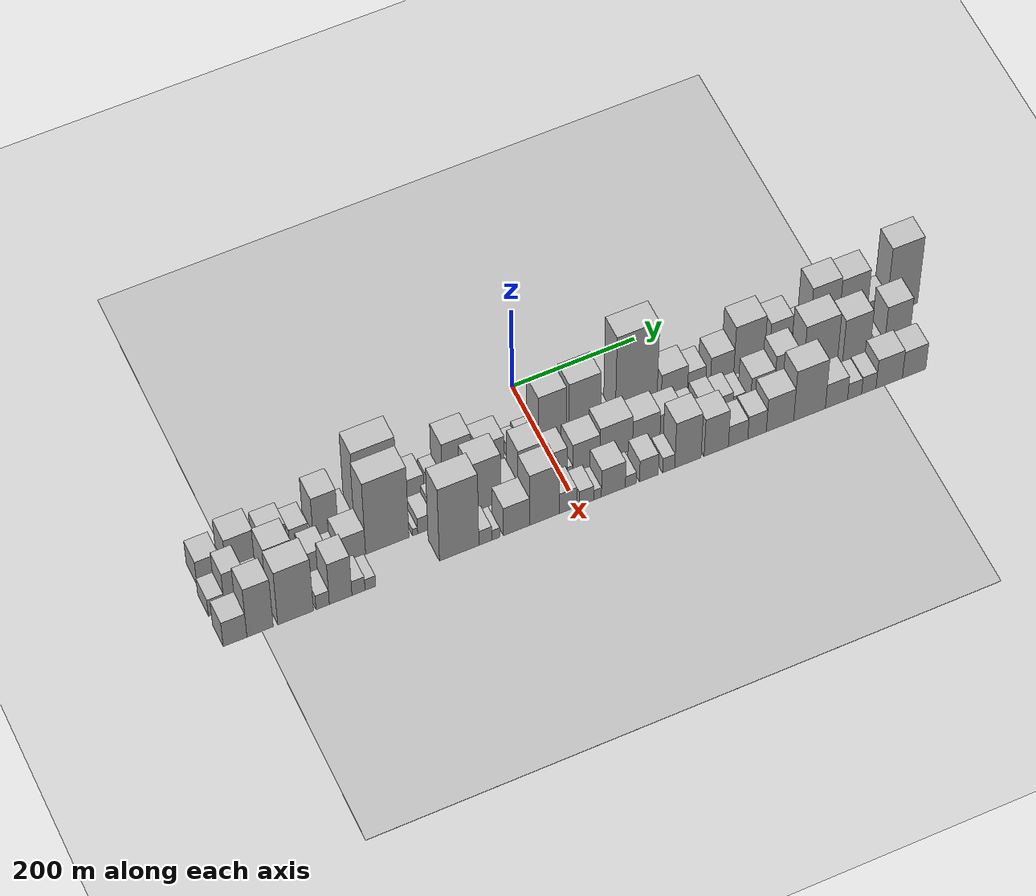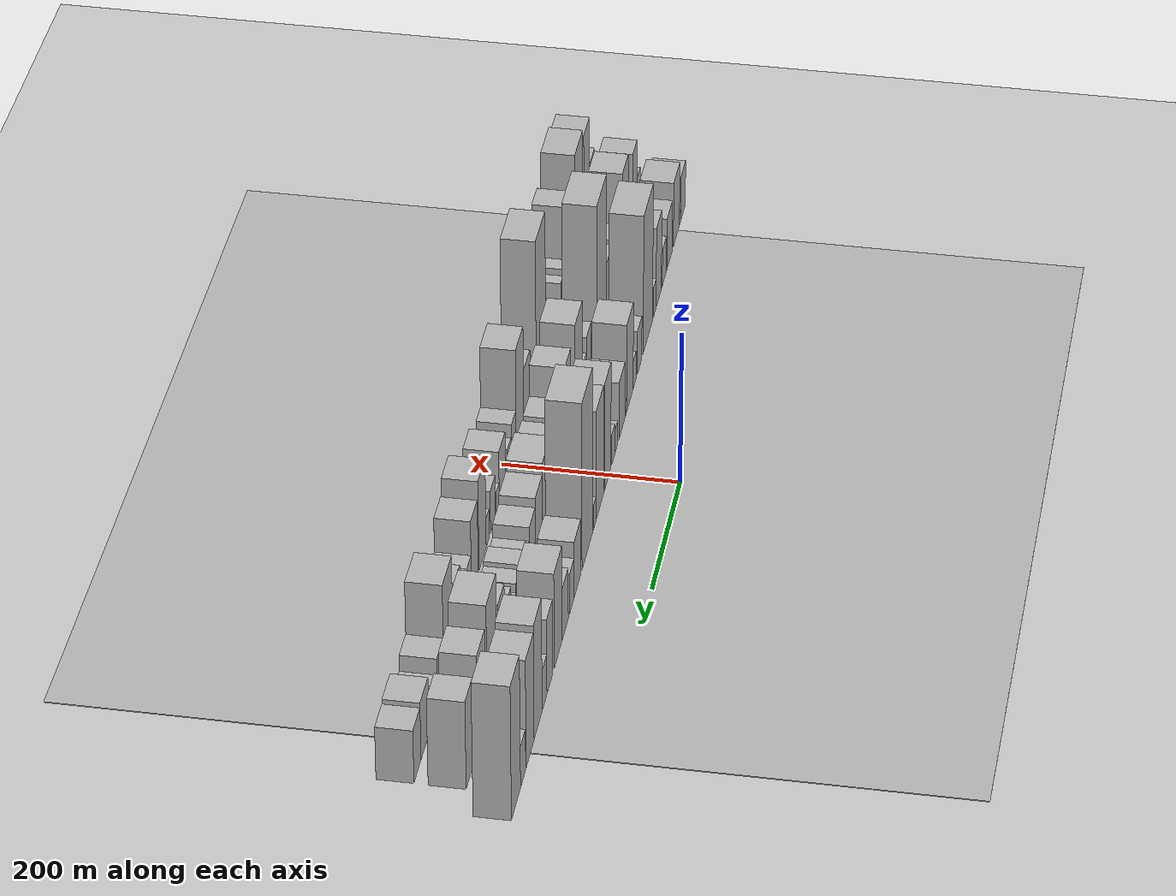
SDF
<?xml version="1.0" encoding="utf-8"?>

<sdf version="1.6">

   <world name="default">

      <gui fullscreen="0">

         <camera name="user_camera">

            <pose>-15 0 4.57585 0 0 0</pose>

            <view_controller>orbit</view_controller>

         </camera>

      </gui>

      <scene>

         <sky>

           <clouds>

             <speed>12</speed>

           </clouds>

         </sky>

         <ambient>0.4 0.4 0.4 1</ambient>

         <background>0.7 0.7 0.7 1</background>

         <shadows>1</shadows>

      </scene>

      <gravity>0 0 -9.8066</gravity>

      <magnetic_field>6e-06 2.3e-05 -4.2e-05</magnetic_field>

      <physics default="0" name="default_physics" type="ode">

         <ode>

            <solver>

               <type>quick</type>

               <iters>10</iters>

               <sor>1.0</sor>

               <use_dynamic_moi_rescaling>0</use_dynamic_moi_rescaling>

            </solver>

            <constraints>

               <cfm>0</cfm>

               <erp>0.2</erp>

               <contact_max_correcting_vel>100</contact_max_correcting_vel>

               <contact_surface_layer>0.001</contact_surface_layer>

            </constraints>

         </ode>

         <max_step_size>0.004</max_step_size>

         <real_time_factor>1</real_time_factor>

         <real_time_update_rate>250</real_time_update_rate>

      </physics>

      <light name="sun" type="directional">

         <cast_shadows>1</cast_shadows>

         <pose>0 0 10 0 0 0</pose>

         <diffuse>0.8 0.8 0.8 1</diffuse>

         <specular>0.2 0.2 0.2 1</specular>

         <attenuation>

            <range>1000</range>

            <constant>0.9</constant>

            <linear>0.01</linear>

            <quadratic>0.001</quadratic>

         </attenuation>

         <direction>-0.5 0.1 -0.9</direction>

      </light>

      <include>

         <name>ground_plane_1</name>

         <uri>model://HANNAS_ground_plane</uri>

         <pose>0 0 0  0 0 0</pose>

      </include>

      <include>

         <name>ground_plane_2</name>

         <uri>model://HANNAS_ground_plane</uri>

         <pose>100 0 0  0 0 0</pose>

      </include>

      <model name="building_1">

         <static>1</static>

         <pose frame="">100.0000 -536.4978 0 0.000000 0.000000 0.000000</pose>

         <link name="link">

            <pose frame="">0 0 31.50 0 0 0</pose>

            <collision name="collision">

               <geometry>

                  <box>

                     <size>40.0000 37.0043 63.0000</size>

                  </box>

               </geometry>

               <max_contacts>10</max_contacts>

               <surface>

                  <contact>

                     <ode/>

                  </contact>

                  <bounce/>

                  <friction>

                     <torsional>

                        <ode/>

                     </torsional>

                     <ode/>

                  </friction>

               </surface>

            </collision>

            <visual name="visual">

               <cast_shadows>0</cast_shadows>

               <geometry>

                  <box>

                     <size>40.0000 37.0043 63.0000</size>

                  </box>

               </geometry>

               <material>

                  <script>

                     <uri>model://HANNAS_wall/materials/scripts</uri>

                     <uri>model://HANNAS_wall/materials/textures</uri>

                     <name>vrc/HANNAS_wall</name>

                  </script>

               </material>

            </visual>

            <self_collide>0</self_collide>

            <enable_wind>0</enable_wind>

            <kinematic>0</kinematic>

         </link>

      </model>

      <model name="building_2">

         <static>1</static>

         <pose frame="">100.0000 -513.5235 0 0.000000 0.000000 0.000000</pose>

         <link name="link">

            <pose frame="">0 0 9.00 0 0 0</pose>

            <collision name="collision">

               <geometry>

                  <box>

                     <size>40.0000 8.9444 18.0000</size>

                  </box>

               </geometry>

               <max_contacts>10</max_contacts>

               <surface>

                  <contact>

                     <ode/>

                  </contact>

                  <bounce/>

                  <friction>

                     <torsional>

                        <ode/>

                     </torsional>

                     <ode/>

                  </friction>

               </surface>

            </collision>

            <visual name="visual">

               <cast_shadows>0</cast_shadows>

               <geometry>

                  <box>

                     <size>40.0000 8.9444 18.0000</size>

                  </box>

               </geometry>

               <material>

                  <script>

                     <uri>model://HANNAS_wall/materials/scripts</uri>

                     <uri>model://HANNAS_wall/materials/textures</uri>

                     <name>vrc/HANNAS_wall</name>

                  </script>

               </material>

            </visual>

            <self_collide>0</self_collide>

            <enable_wind>0</enable_wind>

            <kinematic>0</kinematic>

         </link>

      </model>

      <model name="building_3">

         <static>1</static>

         <pose frame="">100.0000 -485.9807 0 0.000000 0.000000 0.000000</pose>

         <link name="link">

            <pose frame="">0 0 45.00 0 0 0</pose>

            <collision name="collision">

               <geometry>

                  <box>

                     <size>40.0000 46.1410 90.0000</size>

                  </box>

               </geometry>

               <max_contacts>10</max_contacts>

               <surface>

                  <contact>

                     <ode/>

                  </contact>

                  <bounce/>

                  <friction>

                     <torsional>

                        <ode/>

                     </torsional>

                     <ode/>

                  </friction>

               </surface>

            </collision>

            <visual name="visual">

               <cast_shadows>0</cast_shadows>

               <geometry>

                  <box>

                     <size>40.0000 46.1410 90.0000</size>

                  </box>

               </geometry>

               <material>

                  <script>

                     <uri>model://HANNAS_wall/materials/scripts</uri>

                     <uri>model://HANNAS_wall/materials/textures</uri>

                     <name>vrc/HANNAS_wall</name>

                  </script>

               </material>

            </visual>

            <self_collide>0</self_collide>

            <enable_wind>0</enable_wind>

            <kinematic>0</kinematic>

         </link>

      </model>

      <model name="building_4">

         <static>1</static>

         <pose frame="">100.0000 -433.6852 0 0.000000 0.000000 0.000000</pose>

         <link name="link">

            <pose frame="">0 0 36.00 0 0 0</pose>

            <collision name="collision">

               <geometry>

                  <box>

                     <size>40.0000 40.4501 72.0000</size>

                  </box>

               </geometry>

               <max_contacts>10</max_contacts>

               <surface>

                  <contact>

                     <ode/>

                  </contact>

                  <bounce/>

                  <friction>

                     <torsional>

                        <ode/>

                     </torsional>

                     <ode/>

                  </friction>

               </surface>

            </collision>

            <visual name="visual">

               <cast_shadows>0</cast_shadows>

               <geometry>

                  <box>

                     <size>40.0000 40.4501 72.0000</size>

                  </box>

               </geometry>

               <material>

                  <script>

                     <uri>model://HANNAS_wall/materials/scripts</uri>

                     <uri>model://HANNAS_wall/materials/textures</uri>

                     <name>vrc/HANNAS_wall</name>

                  </script>

               </material>

            </visual>

            <self_collide>0</self_collide>

            <enable_wind>0</enable_wind>

            <kinematic>0</kinematic>

         </link>

      </model>

      <model name="building_5">

         <static>1</static>

         <pose frame="">100.0000 -394.5780 0 0.000000 0.000000 0.000000</pose>

         <link name="link">

            <pose frame="">0 0 25.50 0 0 0</pose>

            <collision name="collision">

               <geometry>

                  <box>

                     <size>40.0000 29.7641 51.0000</size>

                  </box>

               </geometry>

               <max_contacts>10</max_contacts>

               <surface>

                  <contact>

                     <ode/>

                  </contact>

                  <bounce/>

                  <friction>

                     <torsional>

                        <ode/>

                     </torsional>

                     <ode/>

                  </friction>

               </surface>

            </collision>

            <visual name="visual">

               <cast_shadows>0</cast_shadows>

               <geometry>

                  <box>

                     <size>40.0000 29.7641 51.0000</size>

                  </box>

               </geometry>

               <material>

                  <script>

                     <uri>model://HANNAS_wall/materials/scripts</uri>

                     <uri>model://HANNAS_wall/materials/textures</uri>

                     <name>vrc/HANNAS_wall</name>

                  </script>

               </material>

            </visual>

            <self_collide>0</self_collide>

            <enable_wind>0</enable_wind>

            <kinematic>0</kinematic>

         </link>

      </model>

      <model name="building_6">

         <static>1</static>

         <pose frame="">100.0000 -375.9999 0 0.000000 0.000000 0.000000</pose>

         <link name="link">

            <pose frame="">0 0 9.00 0 0 0</pose>

            <collision name="collision">

               <geometry>

                  <box>

                     <size>40.0000 7.3922 18.0000</size>

                  </box>

               </geometry>

               <max_contacts>10</max_contacts>

               <surface>

                  <contact>

                     <ode/>

                  </contact>

                  <bounce/>

                  <friction>

                     <torsional>

                        <ode/>

                     </torsional>

                     <ode/>

                  </friction>

               </surface>

            </collision>

            <visual name="visual">

               <cast_shadows>0</cast_shadows>

               <geometry>

                  <box>

                     <size>40.0000 7.3922 18.0000</size>

                  </box>

               </geometry>

               <material>

                  <script>

                     <uri>model://HANNAS_wall/materials/scripts</uri>

                     <uri>model://HANNAS_wall/materials/textures</uri>

                     <name>vrc/HANNAS_wall</name>

                  </script>

               </material>

            </visual>

            <self_collide>0</self_collide>

            <enable_wind>0</enable_wind>

            <kinematic>0</kinematic>

         </link>

      </model>

      <model name="building_7">

         <static>1</static>

         <pose frame="">100.0000 -352.7572 0 0.000000 0.000000 0.000000</pose>

         <link name="link">

            <pose frame="">0 0 55.50 0 0 0</pose>

            <collision name="collision">

               <geometry>

                  <box>

                     <size>40.0000 39.0932 111.0000</size>

                  </box>

               </geometry>

               <max_contacts>10</max_contacts>

               <surface>

                  <contact>

                     <ode/>

                  </contact>

                  <bounce/>

                  <friction>

                     <torsional>

                        <ode/>

                     </torsional>

                     <ode/>

                  </friction>

               </surface>

            </collision>

            <visual name="visual">

               <cast_shadows>0</cast_shadows>

               <geometry>

                  <box>

                     <size>40.0000 39.0932 111.0000</size>

                  </box>

               </geometry>

               <material>

                  <script>

                     <uri>model://HANNAS_wall/materials/scripts</uri>

                     <uri>model://HANNAS_wall/materials/textures</uri>

                     <name>vrc/HANNAS_wall</name>

                  </script>

               </material>

            </visual>

            <self_collide>0</self_collide>

            <enable_wind>0</enable_wind>

            <kinematic>0</kinematic>

         </link>

      </model>

      <model name="building_8">

         <static>1</static>

         <pose frame="">100.0000 -322.6855 0 0.000000 0.000000 0.000000</pose>

         <link name="link">

            <pose frame="">0 0 21.00 0 0 0</pose>

            <collision name="collision">

               <geometry>

                  <box>

                     <size>40.0000 21.0502 42.0000</size>

                  </box>

               </geometry>

               <max_contacts>10</max_contacts>

               <surface>

                  <contact>

                     <ode/>

                  </contact>

                  <bounce/>

                  <friction>

                     <torsional>

                        <ode/>

                     </torsional>

                     <ode/>

                  </friction>

               </surface>

            </collision>

            <visual name="visual">

               <cast_shadows>0</cast_shadows>

               <geometry>

                  <box>

                     <size>40.0000 21.0502 42.0000</size>

                  </box>

               </geometry>

               <material>

                  <script>

                     <uri>model://HANNAS_wall/materials/scripts</uri>

                     <uri>model://HANNAS_wall/materials/textures</uri>

                     <name>vrc/HANNAS_wall</name>

                  </script>

               </material>

            </visual>

            <self_collide>0</self_collide>

            <enable_wind>0</enable_wind>

            <kinematic>0</kinematic>

         </link>

      </model>

      <model name="building_9">

         <static>1</static>

         <pose frame="">100.0000 -273.0492 0 0.000000 0.000000 0.000000</pose>

         <link name="link">

            <pose frame="">0 0 94.50 0 0 0</pose>

            <collision name="collision">

               <geometry>

                  <box>

                     <size>40.0000 68.2222 189.0000</size>

                  </box>

               </geometry>

               <max_contacts>10</max_contacts>

               <surface>

                  <contact>

                     <ode/>

                  </contact>

                  <bounce/>

                  <friction>

                     <torsional>

                        <ode/>

                     </torsional>

                     <ode/>

                  </friction>

               </surface>

            </collision>

            <visual name="visual">

               <cast_shadows>0</cast_shadows>

               <geometry>

                  <box>

                     <size>40.0000 68.2222 189.0000</size>

                  </box>

               </geometry>

               <material>

                  <script>

                     <uri>model://HANNAS_wall/materials/scripts</uri>

                     <uri>model://HANNAS_wall/materials/textures</uri>

                     <name>vrc/HANNAS_wall</name>

                  </script>

               </material>

            </visual>

            <self_collide>0</self_collide>

            <enable_wind>0</enable_wind>

            <kinematic>0</kinematic>

         </link>

      </model>

      <model name="building_10">

         <static>1</static>

         <pose frame="">100.0000 -212.8219 0 0.000000 0.000000 0.000000</pose>

         <link name="link">

            <pose frame="">0 0 30.00 0 0 0</pose>

            <collision name="collision">

               <geometry>

                  <box>

                     <size>40.0000 32.2324 60.0000</size>

                  </box>

               </geometry>

               <max_contacts>10</max_contacts>

               <surface>

                  <contact>

                     <ode/>

                  </contact>

                  <bounce/>

                  <friction>

                     <torsional>

                        <ode/>

                     </torsional>

                     <ode/>

                  </friction>

               </surface>

            </collision>

            <visual name="visual">

               <cast_shadows>0</cast_shadows>

               <geometry>

                  <box>

                     <size>40.0000 32.2324 60.0000</size>

                  </box>

               </geometry>

               <material>

                  <script>

                     <uri>model://HANNAS_wall/materials/scripts</uri>

                     <uri>model://HANNAS_wall/materials/textures</uri>

                     <name>vrc/HANNAS_wall</name>

                  </script>

               </material>

            </visual>

            <self_collide>0</self_collide>

            <enable_wind>0</enable_wind>

            <kinematic>0</kinematic>

         </link>

      </model>

      <model name="building_11">

         <static>1</static>

         <pose frame="">100.0000 -178.1105 0 0.000000 0.000000 0.000000</pose>

         <link name="link">

            <pose frame="">0 0 19.50 0 0 0</pose>

            <collision name="collision">

               <geometry>

                  <box>

                     <size>40.0000 21.1903 39.0000</size>

                  </box>

               </geometry>

               <max_contacts>10</max_contacts>

               <surface>

                  <contact>

                     <ode/>

                  </contact>

                  <bounce/>

                  <friction>

                     <torsional>

                        <ode/>

                     </torsional>

                     <ode/>

                  </friction>

               </surface>

            </collision>

            <visual name="visual">

               <cast_shadows>0</cast_shadows>

               <geometry>

                  <box>

                     <size>40.0000 21.1903 39.0000</size>

                  </box>

               </geometry>

               <material>

                  <script>

                     <uri>model://HANNAS_wall/materials/scripts</uri>

                     <uri>model://HANNAS_wall/materials/textures</uri>

                     <name>vrc/HANNAS_wall</name>

                  </script>

               </material>

            </visual>

            <self_collide>0</self_collide>

            <enable_wind>0</enable_wind>

            <kinematic>0</kinematic>

         </link>

      </model>

      <model name="building_12">

         <static>1</static>

         <pose frame="">100.0000 -144.1233 0 0.000000 0.000000 0.000000</pose>

         <link name="link">

            <pose frame="">0 0 60.00 0 0 0</pose>

            <collision name="collision">

               <geometry>

                  <box>

                     <size>40.0000 46.7842 120.0000</size>

                  </box>

               </geometry>

               <max_contacts>10</max_contacts>

               <surface>

                  <contact>

                     <ode/>

                  </contact>

                  <bounce/>

                  <friction>

                     <torsional>

                        <ode/>

                     </torsional>

                     <ode/>

                  </friction>

               </surface>

            </collision>

            <visual name="visual">

               <cast_shadows>0</cast_shadows>

               <geometry>

                  <box>

                     <size>40.0000 46.7842 120.0000</size>

                  </box>

               </geometry>

               <material>

                  <script>

                     <uri>model://HANNAS_wall/materials/scripts</uri>

                     <uri>model://HANNAS_wall/materials/textures</uri>

                     <name>vrc/HANNAS_wall</name>

                  </script>

               </material>

            </visual>

            <self_collide>0</self_collide>

            <enable_wind>0</enable_wind>

            <kinematic>0</kinematic>

         </link>

      </model>

      <model name="building_13">

         <static>1</static>

         <pose frame="">100.0000 -115.5351 0 0.000000 0.000000 0.000000</pose>

         <link name="link">

            <pose frame="">0 0 10.50 0 0 0</pose>

            <collision name="collision">

               <geometry>

                  <box>

                     <size>40.0000 10.3920 21.0000</size>

                  </box>

               </geometry>

               <max_contacts>10</max_contacts>

               <surface>

                  <contact>

                     <ode/>

                  </contact>

                  <bounce/>

                  <friction>

                     <torsional>

                        <ode/>

                     </torsional>

                     <ode/>

                  </friction>

               </surface>

            </collision>

            <visual name="visual">

               <cast_shadows>0</cast_shadows>

               <geometry>

                  <box>

                     <size>40.0000 10.3920 21.0000</size>

                  </box>

               </geometry>

               <material>

                  <script>

                     <uri>model://HANNAS_wall/materials/scripts</uri>

                     <uri>model://HANNAS_wall/materials/textures</uri>

                     <name>vrc/HANNAS_wall</name>

                  </script>

               </material>

            </visual>

            <self_collide>0</self_collide>

            <enable_wind>0</enable_wind>

            <kinematic>0</kinematic>

         </link>

      </model>

      <model name="building_14">

         <static>1</static>

         <pose frame="">100.0000 -89.1203 0 0.000000 0.000000 0.000000</pose>

         <link name="link">

            <pose frame="">0 0 39.00 0 0 0</pose>

            <collision name="collision">

               <geometry>

                  <box>

                     <size>40.0000 42.4377 78.0000</size>

                  </box>

               </geometry>

               <max_contacts>10</max_contacts>

               <surface>

                  <contact>

                     <ode/>

                  </contact>

                  <bounce/>

                  <friction>

                     <torsional>

                        <ode/>

                     </torsional>

                     <ode/>

                  </friction>

               </surface>

            </collision>

            <visual name="visual">

               <cast_shadows>0</cast_shadows>

               <geometry>

                  <box>

                     <size>40.0000 42.4377 78.0000</size>

                  </box>

               </geometry>

               <material>

                  <script>

                     <uri>model://HANNAS_wall/materials/scripts</uri>

                     <uri>model://HANNAS_wall/materials/textures</uri>

                     <name>vrc/HANNAS_wall</name>

                  </script>

               </material>

            </visual>

            <self_collide>0</self_collide>

            <enable_wind>0</enable_wind>

            <kinematic>0</kinematic>

         </link>

      </model>

      <model name="building_15">

         <static>1</static>

         <pose frame="">100.0000 -49.3917 0 0.000000 0.000000 0.000000</pose>

         <link name="link">

            <pose frame="">0 0 16.50 0 0 0</pose>

            <collision name="collision">

               <geometry>

                  <box>

                     <size>40.0000 19.0196 33.0000</size>

                  </box>

               </geometry>

               <max_contacts>10</max_contacts>

               <surface>

                  <contact>

                     <ode/>

                  </contact>

                  <bounce/>

                  <friction>

                     <torsional>

                        <ode/>

                     </torsional>

                     <ode/>

                  </friction>

               </surface>

            </collision>

            <visual name="visual">

               <cast_shadows>0</cast_shadows>

               <geometry>

                  <box>

                     <size>40.0000 19.0196 33.0000</size>

                  </box>

               </geometry>

               <material>

                  <script>

                     <uri>model://HANNAS_wall/materials/scripts</uri>

                     <uri>model://HANNAS_wall/materials/textures</uri>

                     <name>vrc/HANNAS_wall</name>

                  </script>

               </material>

            </visual>

            <self_collide>0</self_collide>

            <enable_wind>0</enable_wind>

            <kinematic>0</kinematic>

         </link>

      </model>

      <model name="building_16">

         <static>1</static>

         <pose frame="">100.0000 -28.5650 0 0.000000 0.000000 0.000000</pose>

         <link name="link">

            <pose frame="">0 0 21.00 0 0 0</pose>

            <collision name="collision">

               <geometry>

                  <box>

                     <size>40.0000 22.6339 42.0000</size>

                  </box>

               </geometry>

               <max_contacts>10</max_contacts>

               <surface>

                  <contact>

                     <ode/>

                  </contact>

                  <bounce/>

                  <friction>

                     <torsional>

                        <ode/>

                     </torsional>

                     <ode/>

                  </friction>

               </surface>

            </collision>

            <visual name="visual">

               <cast_shadows>0</cast_shadows>

               <geometry>

                  <box>

                     <size>40.0000 22.6339 42.0000</size>

                  </box>

               </geometry>

               <material>

                  <script>

                     <uri>model://HANNAS_wall/materials/scripts</uri>

                     <uri>model://HANNAS_wall/materials/textures</uri>

                     <name>vrc/HANNAS_wall</name>

                  </script>

               </material>

            </visual>

            <self_collide>0</self_collide>

            <enable_wind>0</enable_wind>

            <kinematic>0</kinematic>

         </link>

      </model>

      <model name="building_17">

         <static>1</static>

         <pose frame="">100.0000 9.3949 0 0.000000 0.000000 0.000000</pose>

         <link name="link">

            <pose frame="">0 0 72.00 0 0 0</pose>

            <collision name="collision">

               <geometry>

                  <box>

                     <size>40.0000 45.2859 144.0000</size>

                  </box>

               </geometry>

               <max_contacts>10</max_contacts>

               <surface>

                  <contact>

                     <ode/>

                  </contact>

                  <bounce/>

                  <friction>

                     <torsional>

                        <ode/>

                     </torsional>

                     <ode/>

                  </friction>

               </surface>

            </collision>

            <visual name="visual">

               <cast_shadows>0</cast_shadows>

               <geometry>

                  <box>

                     <size>40.0000 45.2859 144.0000</size>

                  </box>

               </geometry>

               <material>

                  <script>

                     <uri>model://HANNAS_wall/materials/scripts</uri>

                     <uri>model://HANNAS_wall/materials/textures</uri>

                     <name>vrc/HANNAS_wall</name>

                  </script>

               </material>

            </visual>

            <self_collide>0</self_collide>

            <enable_wind>0</enable_wind>

            <kinematic>0</kinematic>

         </link>

      </model>

      <model name="building_18">

         <static>1</static>

         <pose frame="">100.0000 61.7021 0 0.000000 0.000000 0.000000</pose>

         <link name="link">

            <pose frame="">0 0 73.50 0 0 0</pose>

            <collision name="collision">

               <geometry>

                  <box>

                     <size>40.0000 51.3285 147.0000</size>

                  </box>

               </geometry>

               <max_contacts>10</max_contacts>

               <surface>

                  <contact>

                     <ode/>

                  </contact>

                  <bounce/>

                  <friction>

                     <torsional>

                        <ode/>

                     </torsional>

                     <ode/>

                  </friction>

               </surface>

            </collision>

            <visual name="visual">

               <cast_shadows>0</cast_shadows>

               <geometry>

                  <box>

                     <size>40.0000 51.3285 147.0000</size>

                  </box>

               </geometry>

               <material>

                  <script>

                     <uri>model://HANNAS_wall/materials/scripts</uri>

                     <uri>model://HANNAS_wall/materials/textures</uri>

                     <name>vrc/HANNAS_wall</name>

                  </script>

               </material>

            </visual>

            <self_collide>0</self_collide>

            <enable_wind>0</enable_wind>

            <kinematic>0</kinematic>

         </link>

      </model>

      <model name="building_19">

         <static>1</static>

         <pose frame="">100.0000 96.4428 0 0.000000 0.000000 0.000000</pose>

         <link name="link">

            <pose frame="">0 0 16.50 0 0 0</pose>

            <collision name="collision">

               <geometry>

                  <box>

                     <size>40.0000 18.1529 33.0000</size>

                  </box>

               </geometry>

               <max_contacts>10</max_contacts>

               <surface>

                  <contact>

                     <ode/>

                  </contact>

                  <bounce/>

                  <friction>

                     <torsional>

                        <ode/>

                     </torsional>

                     <ode/>

                  </friction>

               </surface>

            </collision>

            <visual name="visual">

               <cast_shadows>0</cast_shadows>

               <geometry>

                  <box>

                     <size>40.0000 18.1529 33.0000</size>

                  </box>

               </geometry>

               <material>

                  <script>

                     <uri>model://HANNAS_wall/materials/scripts</uri>

                     <uri>model://HANNAS_wall/materials/textures</uri>

                     <name>vrc/HANNAS_wall</name>

                  </script>

               </material>

            </visual>

            <self_collide>0</self_collide>

            <enable_wind>0</enable_wind>

            <kinematic>0</kinematic>

         </link>

      </model>

      <model name="building_20">

         <static>1</static>

         <pose frame="">100.0000 145.3928 0 0.000000 0.000000 0.000000</pose>

         <link name="link">

            <pose frame="">0 0 111.00 0 0 0</pose>

            <collision name="collision">

               <geometry>

                  <box>

                     <size>40.0000 67.7470 222.0000</size>

                  </box>

               </geometry>

               <max_contacts>10</max_contacts>

               <surface>

                  <contact>

                     <ode/>

                  </contact>

                  <bounce/>

                  <friction>

                     <torsional>

                        <ode/>

                     </torsional>

                     <ode/>

                  </friction>

               </surface>

            </collision>

            <visual name="visual">

               <cast_shadows>0</cast_shadows>

               <geometry>

                  <box>

                     <size>40.0000 67.7470 222.0000</size>

                  </box>

               </geometry>

               <material>

                  <script>

                     <uri>model://HANNAS_wall/materials/scripts</uri>

                     <uri>model://HANNAS_wall/materials/textures</uri>

                     <name>vrc/HANNAS_wall</name>

                  </script>

               </material>

            </visual>

            <self_collide>0</self_collide>

            <enable_wind>0</enable_wind>

            <kinematic>0</kinematic>

         </link>

      </model>

      <model name="building_21">

         <static>1</static>

         <pose frame="">100.0000 207.8887 0 0.000000 0.000000 0.000000</pose>

         <link name="link">

            <pose frame="">0 0 37.50 0 0 0</pose>

            <collision name="collision">

               <geometry>

                  <box>

                     <size>40.0000 43.2449 75.0000</size>

                  </box>

               </geometry>

               <max_contacts>10</max_contacts>

               <surface>

                  <contact>

                     <ode/>

                  </contact>

                  <bounce/>

                  <friction>

                     <torsional>

                        <ode/>

                     </torsional>

                     <ode/>

                  </friction>

               </surface>

            </collision>

            <visual name="visual">

               <cast_shadows>0</cast_shadows>

               <geometry>

                  <box>

                     <size>40.0000 43.2449 75.0000</size>

                  </box>

               </geometry>

               <material>

                  <script>

                     <uri>model://HANNAS_wall/materials/scripts</uri>

                     <uri>model://HANNAS_wall/materials/textures</uri>

                     <name>vrc/HANNAS_wall</name>

                  </script>

               </material>

            </visual>

            <self_collide>0</self_collide>

            <enable_wind>0</enable_wind>

            <kinematic>0</kinematic>

         </link>

      </model>

      <model name="building_22">

         <static>1</static>

         <pose frame="">100.0000 244.3241 0 0.000000 0.000000 0.000000</pose>

         <link name="link">

            <pose frame="">0 0 27.00 0 0 0</pose>

            <collision name="collision">

               <geometry>

                  <box>

                     <size>40.0000 29.6258 54.0000</size>

                  </box>

               </geometry>

               <max_contacts>10</max_contacts>

               <surface>

                  <contact>

                     <ode/>

                  </contact>

                  <bounce/>

                  <friction>

                     <torsional>

                        <ode/>

                     </torsional>

                     <ode/>

                  </friction>

               </surface>

            </collision>

            <visual name="visual">

               <cast_shadows>0</cast_shadows>

               <geometry>

                  <box>

                     <size>40.0000 29.6258 54.0000</size>

                  </box>

               </geometry>

               <material>

                  <script>

                     <uri>model://HANNAS_wall/materials/scripts</uri>

                     <uri>model://HANNAS_wall/materials/textures</uri>

                     <name>vrc/HANNAS_wall</name>

                  </script>

               </material>

            </visual>

            <self_collide>0</self_collide>

            <enable_wind>0</enable_wind>

            <kinematic>0</kinematic>

         </link>

      </model>

      <model name="building_23">

         <static>1</static>

         <pose frame="">100.0000 286.3577 0 0.000000 0.000000 0.000000</pose>

         <link name="link">

            <pose frame="">0 0 34.50 0 0 0</pose>

            <collision name="collision">

               <geometry>

                  <box>

                     <size>40.0000 38.4415 69.0000</size>

                  </box>

               </geometry>

               <max_contacts>10</max_contacts>

               <surface>

                  <contact>

                     <ode/>

                  </contact>

                  <bounce/>

                  <friction>

                     <torsional>

                        <ode/>

                     </torsional>

                     <ode/>

                  </friction>

               </surface>

            </collision>

            <visual name="visual">

               <cast_shadows>0</cast_shadows>

               <geometry>

                  <box>

                     <size>40.0000 38.4415 69.0000</size>

                  </box>

               </geometry>

               <material>

                  <script>

                     <uri>model://HANNAS_wall/materials/scripts</uri>

                     <uri>model://HANNAS_wall/materials/textures</uri>

                     <name>vrc/HANNAS_wall</name>

                  </script>

               </material>

            </visual>

            <self_collide>0</self_collide>

            <enable_wind>0</enable_wind>

            <kinematic>0</kinematic>

         </link>

      </model>

      <model name="building_24">

         <static>1</static>

         <pose frame="">100.0000 330.7037 0 0.000000 0.000000 0.000000</pose>

         <link name="link">

            <pose frame="">0 0 63.00 0 0 0</pose>

            <collision name="collision">

               <geometry>

                  <box>

                     <size>40.0000 50.2504 126.0000</size>

                  </box>

               </geometry>

               <max_contacts>10</max_contacts>

               <surface>

                  <contact>

                     <ode/>

                  </contact>

                  <bounce/>

                  <friction>

                     <torsional>

                        <ode/>

                     </torsional>

                     <ode/>

                  </friction>

               </surface>

            </collision>

            <visual name="visual">

               <cast_shadows>0</cast_shadows>

               <geometry>

                  <box>

                     <size>40.0000 50.2504 126.0000</size>

                  </box>

               </geometry>

               <material>

                  <script>

                     <uri>model://HANNAS_wall/materials/scripts</uri>

                     <uri>model://HANNAS_wall/materials/textures</uri>

                     <name>vrc/HANNAS_wall</name>

                  </script>

               </material>

            </visual>

            <self_collide>0</self_collide>

            <enable_wind>0</enable_wind>

            <kinematic>0</kinematic>

         </link>

      </model>

      <model name="building_25">

         <static>1</static>

         <pose frame="">100.0000 382.1720 0 0.000000 0.000000 0.000000</pose>

         <link name="link">

            <pose frame="">0 0 49.50 0 0 0</pose>

            <collision name="collision">

               <geometry>

                  <box>

                     <size>40.0000 36.6862 99.0000</size>

                  </box>

               </geometry>

               <max_contacts>10</max_contacts>

               <surface>

                  <contact>

                     <ode/>

                  </contact>

                  <bounce/>

                  <friction>

                     <torsional>

                        <ode/>

                     </torsional>

                     <ode/>

                  </friction>

               </surface>

            </collision>

            <visual name="visual">

               <cast_shadows>0</cast_shadows>

               <geometry>

                  <box>

                     <size>40.0000 36.6862 99.0000</size>

                  </box>

               </geometry>

               <material>

                  <script>

                     <uri>model://HANNAS_wall/materials/scripts</uri>

                     <uri>model://HANNAS_wall/materials/textures</uri>

                     <name>vrc/HANNAS_wall</name>

                  </script>

               </material>

            </visual>

            <self_collide>0</self_collide>

            <enable_wind>0</enable_wind>

            <kinematic>0</kinematic>

         </link>

      </model>

      <model name="building_26">

         <static>1</static>

         <pose frame="">100.0000 415.2358 0 0.000000 0.000000 0.000000</pose>

         <link name="link">

            <pose frame="">0 0 27.00 0 0 0</pose>

            <collision name="collision">

               <geometry>

                  <box>

                     <size>40.0000 29.4415 54.0000</size>

                  </box>

               </geometry>

               <max_contacts>10</max_contacts>

               <surface>

                  <contact>

                     <ode/>

                  </contact>

                  <bounce/>

                  <friction>

                     <torsional>

                        <ode/>

                     </torsional>

                     <ode/>

                  </friction>

               </surface>

            </collision>

            <visual name="visual">

               <cast_shadows>0</cast_shadows>

               <geometry>

                  <box>

                     <size>40.0000 29.4415 54.0000</size>

                  </box>

               </geometry>

               <material>

                  <script>

                     <uri>model://HANNAS_wall/materials/scripts</uri>

                     <uri>model://HANNAS_wall/materials/textures</uri>

                     <name>vrc/HANNAS_wall</name>

                  </script>

               </material>

            </visual>

            <self_collide>0</self_collide>

            <enable_wind>0</enable_wind>

            <kinematic>0</kinematic>

         </link>

      </model>

      <model name="building_27">

         <static>1</static>

         <pose frame="">100.0000 454.1759 0 0.000000 0.000000 0.000000</pose>

         <link name="link">

            <pose frame="">0 0 75.00 0 0 0</pose>

            <collision name="collision">

               <geometry>

                  <box>

                     <size>40.0000 48.4387 150.0000</size>

                  </box>

               </geometry>

               <max_contacts>10</max_contacts>

               <surface>

                  <contact>

                     <ode/>

                  </contact>

                  <bounce/>

                  <friction>

                     <torsional>

                        <ode/>

                     </torsional>

                     <ode/>

                  </friction>

               </surface>

            </collision>

            <visual name="visual">

               <cast_shadows>0</cast_shadows>

               <geometry>

                  <box>

                     <size>40.0000 48.4387 150.0000</size>

                  </box>

               </geometry>

               <material>

                  <script>

                     <uri>model://HANNAS_wall/materials/scripts</uri>

                     <uri>model://HANNAS_wall/materials/textures</uri>

                     <name>vrc/HANNAS_wall</name>

                  </script>

               </material>

            </visual>

            <self_collide>0</self_collide>

            <enable_wind>0</enable_wind>

            <kinematic>0</kinematic>

         </link>

      </model>

      <model name="building_28">

         <static>1</static>

         <pose frame="">100.0000 501.9611 0 0.000000 0.000000 0.000000</pose>

         <link name="link">

            <pose frame="">0 0 70.50 0 0 0</pose>

            <collision name="collision">

               <geometry>

                  <box>

                     <size>40.0000 47.1316 141.0000</size>

                  </box>

               </geometry>

               <max_contacts>10</max_contacts>

               <surface>

                  <contact>

                     <ode/>

                  </contact>

                  <bounce/>

                  <friction>

                     <torsional>

                        <ode/>

                     </torsional>

                     <ode/>

                  </friction>

               </surface>

            </collision>

            <visual name="visual">

               <cast_shadows>0</cast_shadows>

               <geometry>

                  <box>

                     <size>40.0000 47.1316 141.0000</size>

                  </box>

               </geometry>

               <material>

                  <script>

                     <uri>model://HANNAS_wall/materials/scripts</uri>

                     <uri>model://HANNAS_wall/materials/textures</uri>

                     <name>vrc/HANNAS_wall</name>

                  </script>

               </material>

            </visual>

            <self_collide>0</self_collide>

            <enable_wind>0</enable_wind>

            <kinematic>0</kinematic>

         </link>

      </model>

      <model name="building_29">

         <static>1</static>

         <pose frame="">100.0000 543.6830 0 0.000000 0.000000 0.000000</pose>

         <link name="link">

            <pose frame="">0 0 27.00 0 0 0</pose>

            <collision name="collision">

               <geometry>

                  <box>

                     <size>40.0000 30.3123 54.0000</size>

                  </box>

               </geometry>

               <max_contacts>10</max_contacts>

               <surface>

                  <contact>

                     <ode/>

                  </contact>

                  <bounce/>

                  <friction>

                     <torsional>

                        <ode/>

                     </torsional>

                     <ode/>

                  </friction>

               </surface>

            </collision>

            <visual name="visual">

               <cast_shadows>0</cast_shadows>

               <geometry>

                  <box>

                     <size>40.0000 30.3123 54.0000</size>

                  </box>

               </geometry>

               <material>

                  <script>

                     <uri>model://HANNAS_wall/materials/scripts</uri>

                     <uri>model://HANNAS_wall/materials/textures</uri>

                     <name>vrc/HANNAS_wall</name>

                  </script>

               </material>

            </visual>

            <self_collide>0</self_collide>

            <enable_wind>0</enable_wind>

            <kinematic>0</kinematic>

         </link>

      </model>

      <model name="building_30">

         <static>1</static>

         <pose frame="">100.0000 585.3237 0 0.000000 0.000000 0.000000</pose>

         <link name="link">

            <pose frame="">0 0 87.00 0 0 0</pose>

            <collision name="collision">

               <geometry>

                  <box>

                     <size>40.0000 52.9691 174.0000</size>

                  </box>

               </geometry>

               <max_contacts>10</max_contacts>

               <surface>

                  <contact>

                     <ode/>

                  </contact>

                  <bounce/>

                  <friction>

                     <torsional>

                        <ode/>

                     </torsional>

                     <ode/>

                  </friction>

               </surface>

            </collision>

            <visual name="visual">

               <cast_shadows>0</cast_shadows>

               <geometry>

                  <box>

                     <size>40.0000 52.9691 174.0000</size>

                  </box>

               </geometry>

               <material>

                  <script>

                     <uri>model://HANNAS_wall/materials/scripts</uri>

                     <uri>model://HANNAS_wall/materials/textures</uri>

                     <name>vrc/HANNAS_wall</name>

                  </script>

               </material>

            </visual>

            <self_collide>0</self_collide>

            <enable_wind>0</enable_wind>

            <kinematic>0</kinematic>

         </link>

      </model>

      <model name="building_31">

         <static>1</static>

         <pose frame="">155.0000 -547.2666 0 0.000000 0.000000 0.000000</pose>

         <link name="link">

            <pose frame="">0 0 22.50 0 0 0</pose>

            <collision name="collision">

               <geometry>

                  <box>

                     <size>40.0000 25.4667 45.0000</size>

                  </box>

               </geometry>

               <max_contacts>10</max_contacts>

               <surface>

                  <contact>

                     <ode/>

                  </contact>

                  <bounce/>

                  <friction>

                     <torsional>

                        <ode/>

                     </torsional>

                     <ode/>

                  </friction>

               </surface>

            </collision>

            <visual name="visual">

               <cast_shadows>0</cast_shadows>

               <geometry>

                  <box>

                     <size>40.0000 25.4667 45.0000</size>

                  </box>

               </geometry>

               <material>

                  <script>

                     <uri>model://HANNAS_wall/materials/scripts</uri>

                     <uri>model://HANNAS_wall/materials/textures</uri>

                     <name>vrc/HANNAS_wall</name>

                  </script>

               </material>

            </visual>

            <self_collide>0</self_collide>

            <enable_wind>0</enable_wind>

            <kinematic>0</kinematic>

         </link>

      </model>

      <model name="building_32">

         <static>1</static>

         <pose frame="">155.0000 -518.5581 0 0.000000 0.000000 0.000000</pose>

         <link name="link">

            <pose frame="">0 0 49.50 0 0 0</pose>

            <collision name="collision">

               <geometry>

                  <box>

                     <size>40.0000 31.9503 99.0000</size>

                  </box>

               </geometry>

               <max_contacts>10</max_contacts>

               <surface>

                  <contact>

                     <ode/>

                  </contact>

                  <bounce/>

                  <friction>

                     <torsional>

                        <ode/>

                     </torsional>

                     <ode/>

                  </friction>

               </surface>

            </collision>

            <visual name="visual">

               <cast_shadows>0</cast_shadows>

               <geometry>

                  <box>

                     <size>40.0000 31.9503 99.0000</size>

                  </box>

               </geometry>

               <material>

                  <script>

                     <uri>model://HANNAS_wall/materials/scripts</uri>

                     <uri>model://HANNAS_wall/materials/textures</uri>

                     <name>vrc/HANNAS_wall</name>

                  </script>

               </material>

            </visual>

            <self_collide>0</self_collide>

            <enable_wind>0</enable_wind>

            <kinematic>0</kinematic>

         </link>

      </model>

      <model name="building_33">

         <static>1</static>

         <pose frame="">155.0000 -497.5634 0 0.000000 0.000000 0.000000</pose>

         <link name="link">

            <pose frame="">0 0 12.00 0 0 0</pose>

            <collision name="collision">

               <geometry>

                  <box>

                     <size>40.0000 10.0391 24.0000</size>

                  </box>

               </geometry>

               <max_contacts>10</max_contacts>

               <surface>

                  <contact>

                     <ode/>

                  </contact>

                  <bounce/>

                  <friction>

                     <torsional>

                        <ode/>

                     </torsional>

                     <ode/>

                  </friction>

               </surface>

            </collision>

            <visual name="visual">

               <cast_shadows>0</cast_shadows>

               <geometry>

                  <box>

                     <size>40.0000 10.0391 24.0000</size>

                  </box>

               </geometry>

               <material>

                  <script>

                     <uri>model://HANNAS_wall/materials/scripts</uri>

                     <uri>model://HANNAS_wall/materials/textures</uri>

                     <name>vrc/HANNAS_wall</name>

                  </script>

               </material>

            </visual>

            <self_collide>0</self_collide>

            <enable_wind>0</enable_wind>

            <kinematic>0</kinematic>

         </link>

      </model>

      <model name="building_34">

         <static>1</static>

         <pose frame="">155.0000 -481.2529 0 0.000000 0.000000 0.000000</pose>

         <link name="link">

            <pose frame="">0 0 21.00 0 0 0</pose>

            <collision name="collision">

               <geometry>

                  <box>

                     <size>40.0000 22.5821 42.0000</size>

                  </box>

               </geometry>

               <max_contacts>10</max_contacts>

               <surface>

                  <contact>

                     <ode/>

                  </contact>

                  <bounce/>

                  <friction>

                     <torsional>

                        <ode/>

                     </torsional>

                     <ode/>

                  </friction>

               </surface>

            </collision>

            <visual name="visual">

               <cast_shadows>0</cast_shadows>

               <geometry>

                  <box>

                     <size>40.0000 22.5821 42.0000</size>

                  </box>

               </geometry>

               <material>

                  <script>

                     <uri>model://HANNAS_wall/materials/scripts</uri>

                     <uri>model://HANNAS_wall/materials/textures</uri>

                     <name>vrc/HANNAS_wall</name>

                  </script>

               </material>

            </visual>

            <self_collide>0</self_collide>

            <enable_wind>0</enable_wind>

            <kinematic>0</kinematic>

         </link>

      </model>

      <model name="building_35">

         <static>1</static>

         <pose frame="">155.0000 -448.2591 0 0.000000 0.000000 0.000000</pose>

         <link name="link">

            <pose frame="">0 0 60.00 0 0 0</pose>

            <collision name="collision">

               <geometry>

                  <box>

                     <size>40.0000 43.4055 120.0000</size>

                  </box>

               </geometry>

               <max_contacts>10</max_contacts>

               <surface>

                  <contact>

                     <ode/>

                  </contact>

                  <bounce/>

                  <friction>

                     <torsional>

                        <ode/>

                     </torsional>

                     <ode/>

                  </friction>

               </surface>

            </collision>

            <visual name="visual">

               <cast_shadows>0</cast_shadows>

               <geometry>

                  <box>

                     <size>40.0000 43.4055 120.0000</size>

                  </box>

               </geometry>

               <material>

                  <script>

                     <uri>model://HANNAS_wall/materials/scripts</uri>

                     <uri>model://HANNAS_wall/materials/textures</uri>

                     <name>vrc/HANNAS_wall</name>

                  </script>

               </material>

            </visual>

            <self_collide>0</self_collide>

            <enable_wind>0</enable_wind>

            <kinematic>0</kinematic>

         </link>

      </model>

      <model name="building_36">

         <static>1</static>

         <pose frame="">155.0000 -418.0772 0 0.000000 0.000000 0.000000</pose>

         <link name="link">

            <pose frame="">0 0 16.50 0 0 0</pose>

            <collision name="collision">

               <geometry>

                  <box>

                     <size>40.0000 16.9582 33.0000</size>

                  </box>

               </geometry>

               <max_contacts>10</max_contacts>

               <surface>

                  <contact>

                     <ode/>

                  </contact>

                  <bounce/>

                  <friction>

                     <torsional>

                        <ode/>

                     </torsional>

                     <ode/>

                  </friction>

               </surface>

            </collision>

            <visual name="visual">

               <cast_shadows>0</cast_shadows>

               <geometry>

                  <box>

                     <size>40.0000 16.9582 33.0000</size>

                  </box>

               </geometry>

               <material>

                  <script>

                     <uri>model://HANNAS_wall/materials/scripts</uri>

                     <uri>model://HANNAS_wall/materials/textures</uri>

                     <name>vrc/HANNAS_wall</name>

                  </script>

               </material>

            </visual>

            <self_collide>0</self_collide>

            <enable_wind>0</enable_wind>

            <kinematic>0</kinematic>

         </link>

      </model>

      <model name="building_37">

         <static>1</static>

         <pose frame="">155.0000 -389.3531 0 0.000000 0.000000 0.000000</pose>

         <link name="link">

            <pose frame="">0 0 31.50 0 0 0</pose>

            <collision name="collision">

               <geometry>

                  <box>

                     <size>40.0000 32.4898 63.0000</size>

                  </box>

               </geometry>

               <max_contacts>10</max_contacts>

               <surface>

                  <contact>

                     <ode/>

                  </contact>

                  <bounce/>

                  <friction>

                     <torsional>

                        <ode/>

                     </torsional>

                     <ode/>

                  </friction>

               </surface>

            </collision>

            <visual name="visual">

               <cast_shadows>0</cast_shadows>

               <geometry>

                  <box>

                     <size>40.0000 32.4898 63.0000</size>

                  </box>

               </geometry>

               <material>

                  <script>

                     <uri>model://HANNAS_wall/materials/scripts</uri>

                     <uri>model://HANNAS_wall/materials/textures</uri>

                     <name>vrc/HANNAS_wall</name>

                  </script>

               </material>

            </visual>

            <self_collide>0</self_collide>

            <enable_wind>0</enable_wind>

            <kinematic>0</kinematic>

         </link>

      </model>

      <model name="building_38">

         <static>1</static>

         <pose frame="">155.0000 -363.6182 0 0.000000 0.000000 0.000000</pose>

         <link name="link">

            <pose frame="">0 0 16.50 0 0 0</pose>

            <collision name="collision">

               <geometry>

                  <box>

                     <size>40.0000 18.9801 33.0000</size>

                  </box>

               </geometry>

               <max_contacts>10</max_contacts>

               <surface>

                  <contact>

                     <ode/>

                  </contact>

                  <bounce/>

                  <friction>

                     <torsional>

                        <ode/>

                     </torsional>

                     <ode/>

                  </friction>

               </surface>

            </collision>

            <visual name="visual">

               <cast_shadows>0</cast_shadows>

               <geometry>

                  <box>

                     <size>40.0000 18.9801 33.0000</size>

                  </box>

               </geometry>

               <material>

                  <script>

                     <uri>model://HANNAS_wall/materials/scripts</uri>

                     <uri>model://HANNAS_wall/materials/textures</uri>

                     <name>vrc/HANNAS_wall</name>

                  </script>

               </material>

            </visual>

            <self_collide>0</self_collide>

            <enable_wind>0</enable_wind>

            <kinematic>0</kinematic>

         </link>

      </model>

      <model name="building_39">

         <static>1</static>

         <pose frame="">155.0000 -333.9596 0 0.000000 0.000000 0.000000</pose>

         <link name="link">

            <pose frame="">0 0 34.50 0 0 0</pose>

            <collision name="collision">

               <geometry>

                  <box>

                     <size>40.0000 40.3371 69.0000</size>

                  </box>

               </geometry>

               <max_contacts>10</max_contacts>

               <surface>

                  <contact>

                     <ode/>

                  </contact>

                  <bounce/>

                  <friction>

                     <torsional>

                        <ode/>

                     </torsional>

                     <ode/>

                  </friction>

               </surface>

            </collision>

            <visual name="visual">

               <cast_shadows>0</cast_shadows>

               <geometry>

                  <box>

                     <size>40.0000 40.3371 69.0000</size>

                  </box>

               </geometry>

               <material>

                  <script>

                     <uri>model://HANNAS_wall/materials/scripts</uri>

                     <uri>model://HANNAS_wall/materials/textures</uri>

                     <name>vrc/HANNAS_wall</name>

                  </script>

               </material>

            </visual>

            <self_collide>0</self_collide>

            <enable_wind>0</enable_wind>

            <kinematic>0</kinematic>

         </link>

      </model>

      <model name="building_40">

         <static>1</static>

         <pose frame="">155.0000 -279.4858 0 0.000000 0.000000 0.000000</pose>

         <link name="link">

            <pose frame="">0 0 96.00 0 0 0</pose>

            <collision name="collision">

               <geometry>

                  <box>

                     <size>40.0000 68.6106 192.0000</size>

                  </box>

               </geometry>

               <max_contacts>10</max_contacts>

               <surface>

                  <contact>

                     <ode/>

                  </contact>

                  <bounce/>

                  <friction>

                     <torsional>

                        <ode/>

                     </torsional>

                     <ode/>

                  </friction>

               </surface>

            </collision>

            <visual name="visual">

               <cast_shadows>0</cast_shadows>

               <geometry>

                  <box>

                     <size>40.0000 68.6106 192.0000</size>

                  </box>

               </geometry>

               <material>

                  <script>

                     <uri>model://HANNAS_wall/materials/scripts</uri>

                     <uri>model://HANNAS_wall/materials/textures</uri>

                     <name>vrc/HANNAS_wall</name>

                  </script>

               </material>

            </visual>

            <self_collide>0</self_collide>

            <enable_wind>0</enable_wind>

            <kinematic>0</kinematic>

         </link>

      </model>

      <model name="building_41">

         <static>1</static>

         <pose frame="">155.0000 -235.2653 0 0.000000 0.000000 0.000000</pose>

         <link name="link">

            <pose frame="">0 0 9.00 0 0 0</pose>

            <collision name="collision">

               <geometry>

                  <box>

                     <size>40.0000 7.8304 18.0000</size>

                  </box>

               </geometry>

               <max_contacts>10</max_contacts>

               <surface>

                  <contact>

                     <ode/>

                  </contact>

                  <bounce/>

                  <friction>

                     <torsional>

                        <ode/>

                     </torsional>

                     <ode/>

                  </friction>

               </surface>

            </collision>

            <visual name="visual">

               <cast_shadows>0</cast_shadows>

               <geometry>

                  <box>

                     <size>40.0000 7.8304 18.0000</size>

                  </box>

               </geometry>

               <material>

                  <script>

                     <uri>model://HANNAS_wall/materials/scripts</uri>

                     <uri>model://HANNAS_wall/materials/textures</uri>

                     <name>vrc/HANNAS_wall</name>

                  </script>

               </material>

            </visual>

            <self_collide>0</self_collide>

            <enable_wind>0</enable_wind>

            <kinematic>0</kinematic>

         </link>

      </model>

      <model name="building_42">

         <static>1</static>

         <pose frame="">155.0000 -219.8077 0 0.000000 0.000000 0.000000</pose>

         <link name="link">

            <pose frame="">0 0 21.00 0 0 0</pose>

            <collision name="collision">

               <geometry>

                  <box>

                     <size>40.0000 23.0848 42.0000</size>

                  </box>

               </geometry>

               <max_contacts>10</max_contacts>

               <surface>

                  <contact>

                     <ode/>

                  </contact>

                  <bounce/>

                  <friction>

                     <torsional>

                        <ode/>

                     </torsional>

                     <ode/>

                  </friction>

               </surface>

            </collision>

            <visual name="visual">

               <cast_shadows>0</cast_shadows>

               <geometry>

                  <box>

                     <size>40.0000 23.0848 42.0000</size>

                  </box>

               </geometry>

               <material>

                  <script>

                     <uri>model://HANNAS_wall/materials/scripts</uri>

                     <uri>model://HANNAS_wall/materials/textures</uri>

                     <name>vrc/HANNAS_wall</name>

                  </script>

               </material>

            </visual>

            <self_collide>0</self_collide>

            <enable_wind>0</enable_wind>

            <kinematic>0</kinematic>

         </link>

      </model>

      <model name="building_43">

         <static>1</static>

         <pose frame="">155.0000 -192.2204 0 0.000000 0.000000 0.000000</pose>

         <link name="link">

            <pose frame="">0 0 30.00 0 0 0</pose>

            <collision name="collision">

               <geometry>

                  <box>

                     <size>40.0000 32.0897 60.0000</size>

                  </box>

               </geometry>

               <max_contacts>10</max_contacts>

               <surface>

                  <contact>

                     <ode/>

                  </contact>

                  <bounce/>

                  <friction>

                     <torsional>

                        <ode/>

                     </torsional>

                     <ode/>

                  </friction>

               </surface>

            </collision>

            <visual name="visual">

               <cast_shadows>0</cast_shadows>

               <geometry>

                  <box>

                     <size>40.0000 32.0897 60.0000</size>

                  </box>

               </geometry>

               <material>

                  <script>

                     <uri>model://HANNAS_wall/materials/scripts</uri>

                     <uri>model://HANNAS_wall/materials/textures</uri>

                     <name>vrc/HANNAS_wall</name>

                  </script>

               </material>

            </visual>

            <self_collide>0</self_collide>

            <enable_wind>0</enable_wind>

            <kinematic>0</kinematic>

         </link>

      </model>

      <model name="building_44">

         <static>1</static>

         <pose frame="">155.0000 -164.7455 0 0.000000 0.000000 0.000000</pose>

         <link name="link">

            <pose frame="">0 0 19.50 0 0 0</pose>

            <collision name="collision">

               <geometry>

                  <box>

                     <size>40.0000 22.8601 39.0000</size>

                  </box>

               </geometry>

               <max_contacts>10</max_contacts>

               <surface>

                  <contact>

                     <ode/>

                  </contact>

                  <bounce/>

                  <friction>

                     <torsional>

                        <ode/>

                     </torsional>

                     <ode/>

                  </friction>

               </surface>

            </collision>

            <visual name="visual">

               <cast_shadows>0</cast_shadows>

               <geometry>

                  <box>

                     <size>40.0000 22.8601 39.0000</size>

                  </box>

               </geometry>

               <material>

                  <script>

                     <uri>model://HANNAS_wall/materials/scripts</uri>

                     <uri>model://HANNAS_wall/materials/textures</uri>

                     <name>vrc/HANNAS_wall</name>

                  </script>

               </material>

            </visual>

            <self_collide>0</self_collide>

            <enable_wind>0</enable_wind>

            <kinematic>0</kinematic>

         </link>

      </model>

      <model name="building_45">

         <static>1</static>

         <pose frame="">155.0000 -122.9405 0 0.000000 0.000000 0.000000</pose>

         <link name="link">

            <pose frame="">0 0 64.50 0 0 0</pose>

            <collision name="collision">

               <geometry>

                  <box>

                     <size>40.0000 48.7498 129.0000</size>

                  </box>

               </geometry>

               <max_contacts>10</max_contacts>

               <surface>

                  <contact>

                     <ode/>

                  </contact>

                  <bounce/>

                  <friction>

                     <torsional>

                        <ode/>

                     </torsional>

                     <ode/>

                  </friction>

               </surface>

            </collision>

            <visual name="visual">

               <cast_shadows>0</cast_shadows>

               <geometry>

                  <box>

                     <size>40.0000 48.7498 129.0000</size>

                  </box>

               </geometry>

               <material>

                  <script>

                     <uri>model://HANNAS_wall/materials/scripts</uri>

                     <uri>model://HANNAS_wall/materials/textures</uri>

                     <name>vrc/HANNAS_wall</name>

                  </script>

               </material>

            </visual>

            <self_collide>0</self_collide>

            <enable_wind>0</enable_wind>

            <kinematic>0</kinematic>

         </link>

      </model>

      <model name="building_46">

         <static>1</static>

         <pose frame="">155.0000 -86.2592 0 0.000000 0.000000 0.000000</pose>

         <link name="link">

            <pose frame="">0 0 22.50 0 0 0</pose>

            <collision name="collision">

               <geometry>

                  <box>

                     <size>40.0000 24.6128 45.0000</size>

                  </box>

               </geometry>

               <max_contacts>10</max_contacts>

               <surface>

                  <contact>

                     <ode/>

                  </contact>

                  <bounce/>

                  <friction>

                     <torsional>

                        <ode/>

                     </torsional>

                     <ode/>

                  </friction>

               </surface>

            </collision>

            <visual name="visual">

               <cast_shadows>0</cast_shadows>

               <geometry>

                  <box>

                     <size>40.0000 24.6128 45.0000</size>

                  </box>

               </geometry>

               <material>

                  <script>

                     <uri>model://HANNAS_wall/materials/scripts</uri>

                     <uri>model://HANNAS_wall/materials/textures</uri>

                     <name>vrc/HANNAS_wall</name>

                  </script>

               </material>

            </visual>

            <self_collide>0</self_collide>

            <enable_wind>0</enable_wind>

            <kinematic>0</kinematic>

         </link>

      </model>

      <model name="building_47">

         <static>1</static>

         <pose frame="">155.0000 -50.9392 0 0.000000 0.000000 0.000000</pose>

         <link name="link">

            <pose frame="">0 0 58.50 0 0 0</pose>

            <collision name="collision">

               <geometry>

                  <box>

                     <size>40.0000 40.0271 117.0000</size>

                  </box>

               </geometry>

               <max_contacts>10</max_contacts>

               <surface>

                  <contact>

                     <ode/>

                  </contact>

                  <bounce/>

                  <friction>

                     <torsional>

                        <ode/>

                     </torsional>

                     <ode/>

                  </friction>

               </surface>

            </collision>

            <visual name="visual">

               <cast_shadows>0</cast_shadows>

               <geometry>

                  <box>

                     <size>40.0000 40.0271 117.0000</size>

                  </box>

               </geometry>

               <material>

                  <script>

                     <uri>model://HANNAS_wall/materials/scripts</uri>

                     <uri>model://HANNAS_wall/materials/textures</uri>

                     <name>vrc/HANNAS_wall</name>

                  </script>

               </material>

            </visual>

            <self_collide>0</self_collide>

            <enable_wind>0</enable_wind>

            <kinematic>0</kinematic>

         </link>

      </model>

      <model name="building_48">

         <static>1</static>

         <pose frame="">155.0000 -11.4547 0 0.000000 0.000000 0.000000</pose>

         <link name="link">

            <pose frame="">0 0 37.50 0 0 0</pose>

            <collision name="collision">

               <geometry>

                  <box>

                     <size>40.0000 38.9421 75.0000</size>

                  </box>

               </geometry>

               <max_contacts>10</max_contacts>

               <surface>

                  <contact>

                     <ode/>

                  </contact>

                  <bounce/>

                  <friction>

                     <torsional>

                        <ode/>

                     </torsional>

                     <ode/>

                  </friction>

               </surface>

            </collision>

            <visual name="visual">

               <cast_shadows>0</cast_shadows>

               <geometry>

                  <box>

                     <size>40.0000 38.9421 75.0000</size>

                  </box>

               </geometry>

               <material>

                  <script>

                     <uri>model://HANNAS_wall/materials/scripts</uri>

                     <uri>model://HANNAS_wall/materials/textures</uri>

                     <name>vrc/HANNAS_wall</name>

                  </script>

               </material>

            </visual>

            <self_collide>0</self_collide>

            <enable_wind>0</enable_wind>

            <kinematic>0</kinematic>

         </link>

      </model>

      <model name="building_49">

         <static>1</static>

         <pose frame="">155.0000 12.3418 0 0.000000 0.000000 0.000000</pose>

         <link name="link">

            <pose frame="">0 0 10.50 0 0 0</pose>

            <collision name="collision">

               <geometry>

                  <box>

                     <size>40.0000 8.6510 21.0000</size>

                  </box>

               </geometry>

               <max_contacts>10</max_contacts>

               <surface>

                  <contact>

                     <ode/>

                  </contact>

                  <bounce/>

                  <friction>

                     <torsional>

                        <ode/>

                     </torsional>

                     <ode/>

                  </friction>

               </surface>

            </collision>

            <visual name="visual">

               <cast_shadows>0</cast_shadows>

               <geometry>

                  <box>

                     <size>40.0000 8.6510 21.0000</size>

                  </box>

               </geometry>

               <material>

                  <script>

                     <uri>model://HANNAS_wall/materials/scripts</uri>

                     <uri>model://HANNAS_wall/materials/textures</uri>

                     <name>vrc/HANNAS_wall</name>

                  </script>

               </material>

            </visual>

            <self_collide>0</self_collide>

            <enable_wind>0</enable_wind>

            <kinematic>0</kinematic>

         </link>

      </model>

      <model name="building_50">

         <static>1</static>

         <pose frame="">155.0000 38.7052 0 0.000000 0.000000 0.000000</pose>

         <link name="link">

            <pose frame="">0 0 37.50 0 0 0</pose>

            <collision name="collision">

               <geometry>

                  <box>

                     <size>40.0000 44.0758 75.0000</size>

                  </box>

               </geometry>

               <max_contacts>10</max_contacts>

               <surface>

                  <contact>

                     <ode/>

                  </contact>

                  <bounce/>

                  <friction>

                     <torsional>

                        <ode/>

                     </torsional>

                     <ode/>

                  </friction>

               </surface>

            </collision>

            <visual name="visual">

               <cast_shadows>0</cast_shadows>

               <geometry>

                  <box>

                     <size>40.0000 44.0758 75.0000</size>

                  </box>

               </geometry>

               <material>

                  <script>

                     <uri>model://HANNAS_wall/materials/scripts</uri>

                     <uri>model://HANNAS_wall/materials/textures</uri>

                     <name>vrc/HANNAS_wall</name>

                  </script>

               </material>

            </visual>

            <self_collide>0</self_collide>

            <enable_wind>0</enable_wind>

            <kinematic>0</kinematic>

         </link>

      </model>

      <model name="building_51">

         <static>1</static>

         <pose frame="">155.0000 87.0932 0 0.000000 0.000000 0.000000</pose>

         <link name="link">

            <pose frame="">0 0 45.00 0 0 0</pose>

            <collision name="collision">

               <geometry>

                  <box>

                     <size>40.0000 52.7002 90.0000</size>

                  </box>

               </geometry>

               <max_contacts>10</max_contacts>

               <surface>

                  <contact>

                     <ode/>

                  </contact>

                  <bounce/>

                  <friction>

                     <torsional>

                        <ode/>

                     </torsional>

                     <ode/>

                  </friction>

               </surface>

            </collision>

            <visual name="visual">

               <cast_shadows>0</cast_shadows>

               <geometry>

                  <box>

                     <size>40.0000 52.7002 90.0000</size>

                  </box>

               </geometry>

               <material>

                  <script>

                     <uri>model://HANNAS_wall/materials/scripts</uri>

                     <uri>model://HANNAS_wall/materials/textures</uri>

                     <name>vrc/HANNAS_wall</name>

                  </script>

               </material>

            </visual>

            <self_collide>0</self_collide>

            <enable_wind>0</enable_wind>

            <kinematic>0</kinematic>

         </link>

      </model>

      <model name="building_52">

         <static>1</static>

         <pose frame="">155.0000 135.7613 0 0.000000 0.000000 0.000000</pose>

         <link name="link">

            <pose frame="">0 0 37.50 0 0 0</pose>

            <collision name="collision">

               <geometry>

                  <box>

                     <size>40.0000 44.6360 75.0000</size>

                  </box>

               </geometry>

               <max_contacts>10</max_contacts>

               <surface>

                  <contact>

                     <ode/>

                  </contact>

                  <bounce/>

                  <friction>

                     <torsional>

                        <ode/>

                     </torsional>

                     <ode/>

                  </friction>

               </surface>

            </collision>

            <visual name="visual">

               <cast_shadows>0</cast_shadows>

               <geometry>

                  <box>

                     <size>40.0000 44.6360 75.0000</size>

                  </box>

               </geometry>

               <material>

                  <script>

                     <uri>model://HANNAS_wall/materials/scripts</uri>

                     <uri>model://HANNAS_wall/materials/textures</uri>

                     <name>vrc/HANNAS_wall</name>

                  </script>

               </material>

            </visual>

            <self_collide>0</self_collide>

            <enable_wind>0</enable_wind>

            <kinematic>0</kinematic>

         </link>

      </model>

      <model name="building_53">

         <static>1</static>

         <pose frame="">155.0000 176.6561 0 0.000000 0.000000 0.000000</pose>

         <link name="link">

            <pose frame="">0 0 31.50 0 0 0</pose>

            <collision name="collision">

               <geometry>

                  <box>

                     <size>40.0000 37.1536 63.0000</size>

                  </box>

               </geometry>

               <max_contacts>10</max_contacts>

               <surface>

                  <contact>

                     <ode/>

                  </contact>

                  <bounce/>

                  <friction>

                     <torsional>

                        <ode/>

                     </torsional>

                     <ode/>

                  </friction>

               </surface>

            </collision>

            <visual name="visual">

               <cast_shadows>0</cast_shadows>

               <geometry>

                  <box>

                     <size>40.0000 37.1536 63.0000</size>

                  </box>

               </geometry>

               <material>

                  <script>

                     <uri>model://HANNAS_wall/materials/scripts</uri>

                     <uri>model://HANNAS_wall/materials/textures</uri>

                     <name>vrc/HANNAS_wall</name>

                  </script>

               </material>

            </visual>

            <self_collide>0</self_collide>

            <enable_wind>0</enable_wind>

            <kinematic>0</kinematic>

         </link>

      </model>

      <model name="building_54">

         <static>1</static>

         <pose frame="">155.0000 207.8142 0 0.000000 0.000000 0.000000</pose>

         <link name="link">

            <pose frame="">0 0 22.50 0 0 0</pose>

            <collision name="collision">

               <geometry>

                  <box>

                     <size>40.0000 25.1626 45.0000</size>

                  </box>

               </geometry>

               <max_contacts>10</max_contacts>

               <surface>

                  <contact>

                     <ode/>

                  </contact>

                  <bounce/>

                  <friction>

                     <torsional>

                        <ode/>

                     </torsional>

                     <ode/>

                  </friction>

               </surface>

            </collision>

            <visual name="visual">

               <cast_shadows>0</cast_shadows>

               <geometry>

                  <box>

                     <size>40.0000 25.1626 45.0000</size>

                  </box>

               </geometry>

               <material>

                  <script>

                     <uri>model://HANNAS_wall/materials/scripts</uri>

                     <uri>model://HANNAS_wall/materials/textures</uri>

                     <name>vrc/HANNAS_wall</name>

                  </script>

               </material>

            </visual>

            <self_collide>0</self_collide>

            <enable_wind>0</enable_wind>

            <kinematic>0</kinematic>

         </link>

      </model>

      <model name="building_55">

         <static>1</static>

         <pose frame="">155.0000 237.3686 0 0.000000 0.000000 0.000000</pose>

         <link name="link">

            <pose frame="">0 0 27.00 0 0 0</pose>

            <collision name="collision">

               <geometry>

                  <box>

                     <size>40.0000 27.9462 54.0000</size>

                  </box>

               </geometry>

               <max_contacts>10</max_contacts>

               <surface>

                  <contact>

                     <ode/>

                  </contact>

                  <bounce/>

                  <friction>

                     <torsional>

                        <ode/>

                     </torsional>

                     <ode/>

                  </friction>

               </surface>

            </collision>

            <visual name="visual">

               <cast_shadows>0</cast_shadows>

               <geometry>

                  <box>

                     <size>40.0000 27.9462 54.0000</size>

                  </box>

               </geometry>

               <material>

                  <script>

                     <uri>model://HANNAS_wall/materials/scripts</uri>

                     <uri>model://HANNAS_wall/materials/textures</uri>

                     <name>vrc/HANNAS_wall</name>

                  </script>

               </material>

            </visual>

            <self_collide>0</self_collide>

            <enable_wind>0</enable_wind>

            <kinematic>0</kinematic>

         </link>

      </model>

      <model name="building_56">

         <static>1</static>

         <pose frame="">155.0000 264.2852 0 0.000000 0.000000 0.000000</pose>

         <link name="link">

            <pose frame="">0 0 24.00 0 0 0</pose>

            <collision name="collision">

               <geometry>

                  <box>

                     <size>40.0000 25.8870 48.0000</size>

                  </box>

               </geometry>

               <max_contacts>10</max_contacts>

               <surface>

                  <contact>

                     <ode/>

                  </contact>

                  <bounce/>

                  <friction>

                     <torsional>

                        <ode/>

                     </torsional>

                     <ode/>

                  </friction>

               </surface>

            </collision>

            <visual name="visual">

               <cast_shadows>0</cast_shadows>

               <geometry>

                  <box>

                     <size>40.0000 25.8870 48.0000</size>

                  </box>

               </geometry>

               <material>

                  <script>

                     <uri>model://HANNAS_wall/materials/scripts</uri>

                     <uri>model://HANNAS_wall/materials/textures</uri>

                     <name>vrc/HANNAS_wall</name>

                  </script>

               </material>

            </visual>

            <self_collide>0</self_collide>

            <enable_wind>0</enable_wind>

            <kinematic>0</kinematic>

         </link>

      </model>

      <model name="building_57">

         <static>1</static>

         <pose frame="">155.0000 287.2711 0 0.000000 0.000000 0.000000</pose>

         <link name="link">

            <pose frame="">0 0 18.00 0 0 0</pose>

            <collision name="collision">

               <geometry>

                  <box>

                     <size>40.0000 20.0847 36.0000</size>

                  </box>

               </geometry>

               <max_contacts>10</max_contacts>

               <surface>

                  <contact>

                     <ode/>

                  </contact>

                  <bounce/>

                  <friction>

                     <torsional>

                        <ode/>

                     </torsional>

                     <ode/>

                  </friction>

               </surface>

            </collision>

            <visual name="visual">

               <cast_shadows>0</cast_shadows>

               <geometry>

                  <box>

                     <size>40.0000 20.0847 36.0000</size>

                  </box>

               </geometry>

               <material>

                  <script>

                     <uri>model://HANNAS_wall/materials/scripts</uri>

                     <uri>model://HANNAS_wall/materials/textures</uri>

                     <name>vrc/HANNAS_wall</name>

                  </script>

               </material>

            </visual>

            <self_collide>0</self_collide>

            <enable_wind>0</enable_wind>

            <kinematic>0</kinematic>

         </link>

      </model>

      <model name="building_58">

         <static>1</static>

         <pose frame="">155.0000 325.8514 0 0.000000 0.000000 0.000000</pose>

         <link name="link">

            <pose frame="">0 0 33.00 0 0 0</pose>

            <collision name="collision">

               <geometry>

                  <box>

                     <size>40.0000 39.0759 66.0000</size>

                  </box>

               </geometry>

               <max_contacts>10</max_contacts>

               <surface>

                  <contact>

                     <ode/>

                  </contact>

                  <bounce/>

                  <friction>

                     <torsional>

                        <ode/>

                     </torsional>

                     <ode/>

                  </friction>

               </surface>

            </collision>

            <visual name="visual">

               <cast_shadows>0</cast_shadows>

               <geometry>

                  <box>

                     <size>40.0000 39.0759 66.0000</size>

                  </box>

               </geometry>

               <material>

                  <script>

                     <uri>model://HANNAS_wall/materials/scripts</uri>

                     <uri>model://HANNAS_wall/materials/textures</uri>

                     <name>vrc/HANNAS_wall</name>

                  </script>

               </material>

            </visual>

            <self_collide>0</self_collide>

            <enable_wind>0</enable_wind>

            <kinematic>0</kinematic>

         </link>

      </model>

      <model name="building_59">

         <static>1</static>

         <pose frame="">155.0000 364.3384 0 0.000000 0.000000 0.000000</pose>

         <link name="link">

            <pose frame="">0 0 49.50 0 0 0</pose>

            <collision name="collision">

               <geometry>

                  <box>

                     <size>40.0000 37.8981 99.0000</size>

                  </box>

               </geometry>

               <max_contacts>10</max_contacts>

               <surface>

                  <contact>

                     <ode/>

                  </contact>

                  <bounce/>

                  <friction>

                     <torsional>

                        <ode/>

                     </torsional>

                     <ode/>

                  </friction>

               </surface>

            </collision>

            <visual name="visual">

               <cast_shadows>0</cast_shadows>

               <geometry>

                  <box>

                     <size>40.0000 37.8981 99.0000</size>

                  </box>

               </geometry>

               <material>

                  <script>

                     <uri>model://HANNAS_wall/materials/scripts</uri>

                     <uri>model://HANNAS_wall/materials/textures</uri>

                     <name>vrc/HANNAS_wall</name>

                  </script>

               </material>

            </visual>

            <self_collide>0</self_collide>

            <enable_wind>0</enable_wind>

            <kinematic>0</kinematic>

         </link>

      </model>

      <model name="building_60">

         <static>1</static>

         <pose frame="">155.0000 387.7461 0 0.000000 0.000000 0.000000</pose>

         <link name="link">

            <pose frame="">0 0 10.50 0 0 0</pose>

            <collision name="collision">

               <geometry>

                  <box>

                     <size>40.0000 8.9174 21.0000</size>

                  </box>

               </geometry>

               <max_contacts>10</max_contacts>

               <surface>

                  <contact>

                     <ode/>

                  </contact>

                  <bounce/>

                  <friction>

                     <torsional>

                        <ode/>

                     </torsional>

                     <ode/>

                  </friction>

               </surface>

            </collision>

            <visual name="visual">

               <cast_shadows>0</cast_shadows>

               <geometry>

                  <box>

                     <size>40.0000 8.9174 21.0000</size>

                  </box>

               </geometry>

               <material>

                  <script>

                     <uri>model://HANNAS_wall/materials/scripts</uri>

                     <uri>model://HANNAS_wall/materials/textures</uri>

                     <name>vrc/HANNAS_wall</name>

                  </script>

               </material>

            </visual>

            <self_collide>0</self_collide>

            <enable_wind>0</enable_wind>

            <kinematic>0</kinematic>

         </link>

      </model>

      <model name="building_61">

         <static>1</static>

         <pose frame="">155.0000 420.4338 0 0.000000 0.000000 0.000000</pose>

         <link name="link">

            <pose frame="">0 0 73.50 0 0 0</pose>

            <collision name="collision">

               <geometry>

                  <box>

                     <size>40.0000 56.4580 147.0000</size>

                  </box>

               </geometry>

               <max_contacts>10</max_contacts>

               <surface>

                  <contact>

                     <ode/>

                  </contact>

                  <bounce/>

                  <friction>

                     <torsional>

                        <ode/>

                     </torsional>

                     <ode/>

                  </friction>

               </surface>

            </collision>

            <visual name="visual">

               <cast_shadows>0</cast_shadows>

               <geometry>

                  <box>

                     <size>40.0000 56.4580 147.0000</size>

                  </box>

               </geometry>

               <material>

                  <script>

                     <uri>model://HANNAS_wall/materials/scripts</uri>

                     <uri>model://HANNAS_wall/materials/textures</uri>

                     <name>vrc/HANNAS_wall</name>

                  </script>

               </material>

            </visual>

            <self_collide>0</self_collide>

            <enable_wind>0</enable_wind>

            <kinematic>0</kinematic>

         </link>

      </model>

      <model name="building_62">

         <static>1</static>

         <pose frame="">155.0000 480.4092 0 0.000000 0.000000 0.000000</pose>

         <link name="link">

            <pose frame="">0 0 61.50 0 0 0</pose>

            <collision name="collision">

               <geometry>

                  <box>

                     <size>40.0000 45.4929 123.0000</size>

                  </box>

               </geometry>

               <max_contacts>10</max_contacts>

               <surface>

                  <contact>

                     <ode/>

                  </contact>

                  <bounce/>

                  <friction>

                     <torsional>

                        <ode/>

                     </torsional>

                     <ode/>

                  </friction>

               </surface>

            </collision>

            <visual name="visual">

               <cast_shadows>0</cast_shadows>

               <geometry>

                  <box>

                     <size>40.0000 45.4929 123.0000</size>

                  </box>

               </geometry>

               <material>

                  <script>

                     <uri>model://HANNAS_wall/materials/scripts</uri>

                     <uri>model://HANNAS_wall/materials/textures</uri>

                     <name>vrc/HANNAS_wall</name>

                  </script>

               </material>

            </visual>

            <self_collide>0</self_collide>

            <enable_wind>0</enable_wind>

            <kinematic>0</kinematic>

         </link>

      </model>

      <model name="building_63">

         <static>1</static>

         <pose frame="">155.0000 509.0724 0 0.000000 0.000000 0.000000</pose>

         <link name="link">

            <pose frame="">0 0 13.50 0 0 0</pose>

            <collision name="collision">

               <geometry>

                  <box>

                     <size>40.0000 11.8335 27.0000</size>

                  </box>

               </geometry>

               <max_contacts>10</max_contacts>

               <surface>

                  <contact>

                     <ode/>

                  </contact>

                  <bounce/>

                  <friction>

                     <torsional>

                        <ode/>

                     </torsional>

                     <ode/>

                  </friction>

               </surface>

            </collision>

            <visual name="visual">

               <cast_shadows>0</cast_shadows>

               <geometry>

                  <box>

                     <size>40.0000 11.8335 27.0000</size>

                  </box>

               </geometry>

               <material>

                  <script>

                     <uri>model://HANNAS_wall/materials/scripts</uri>

                     <uri>model://HANNAS_wall/materials/textures</uri>

                     <name>vrc/HANNAS_wall</name>

                  </script>

               </material>

            </visual>

            <self_collide>0</self_collide>

            <enable_wind>0</enable_wind>

            <kinematic>0</kinematic>

         </link>

      </model>

      <model name="building_64">

         <static>1</static>

         <pose frame="">155.0000 521.1236 0 0.000000 0.000000 0.000000</pose>

         <link name="link">

            <pose frame="">0 0 13.50 0 0 0</pose>

            <collision name="collision">

               <geometry>

                  <box>

                     <size>40.0000 12.2689 27.0000</size>

                  </box>

               </geometry>

               <max_contacts>10</max_contacts>

               <surface>

                  <contact>

                     <ode/>

                  </contact>

                  <bounce/>

                  <friction>

                     <torsional>

                        <ode/>

                     </torsional>

                     <ode/>

                  </friction>

               </surface>

            </collision>

            <visual name="visual">

               <cast_shadows>0</cast_shadows>

               <geometry>

                  <box>

                     <size>40.0000 12.2689 27.0000</size>

                  </box>

               </geometry>

               <material>

                  <script>

                     <uri>model://HANNAS_wall/materials/scripts</uri>

                     <uri>model://HANNAS_wall/materials/textures</uri>

                     <name>vrc/HANNAS_wall</name>

                  </script>

               </material>

            </visual>

            <self_collide>0</self_collide>

            <enable_wind>0</enable_wind>

            <kinematic>0</kinematic>

         </link>

      </model>

      <model name="building_65">

         <static>1</static>

         <pose frame="">155.0000 548.3630 0 0.000000 0.000000 0.000000</pose>

         <link name="link">

            <pose frame="">0 0 57.00 0 0 0</pose>

            <collision name="collision">

               <geometry>

                  <box>

                     <size>40.0000 42.2099 114.0000</size>

                  </box>

               </geometry>

               <max_contacts>10</max_contacts>

               <surface>

                  <contact>

                     <ode/>

                  </contact>

                  <bounce/>

                  <friction>

                     <torsional>

                        <ode/>

                     </torsional>

                     <ode/>

                  </friction>

               </surface>

            </collision>

            <visual name="visual">

               <cast_shadows>0</cast_shadows>

               <geometry>

                  <box>

                     <size>40.0000 42.2099 114.0000</size>

                  </box>

               </geometry>

               <material>

                  <script>

                     <uri>model://HANNAS_wall/materials/scripts</uri>

                     <uri>model://HANNAS_wall/materials/textures</uri>

                     <name>vrc/HANNAS_wall</name>

                  </script>

               </material>

            </visual>

            <self_collide>0</self_collide>

            <enable_wind>0</enable_wind>

            <kinematic>0</kinematic>

         </link>

      </model>

      <model name="building_66">

         <static>1</static>

         <pose frame="">210.0000 -541.5973 0 0.000000 0.000000 0.000000</pose>

         <link name="link">

            <pose frame="">0 0 33.00 0 0 0</pose>

            <collision name="collision">

               <geometry>

                  <box>

                     <size>40.0000 36.8053 66.0000</size>

                  </box>

               </geometry>

               <max_contacts>10</max_contacts>

               <surface>

                  <contact>

                     <ode/>

                  </contact>

                  <bounce/>

                  <friction>

                     <torsional>

                        <ode/>

                     </torsional>

                     <ode/>

                  </friction>

               </surface>

            </collision>

            <visual name="visual">

               <cast_shadows>0</cast_shadows>

               <geometry>

                  <box>

                     <size>40.0000 36.8053 66.0000</size>

                  </box>

               </geometry>

               <material>

                  <script>

                     <uri>model://HANNAS_wall/materials/scripts</uri>

                     <uri>model://HANNAS_wall/materials/textures</uri>

                     <name>vrc/HANNAS_wall</name>

                  </script>

               </material>

            </visual>

            <self_collide>0</self_collide>

            <enable_wind>0</enable_wind>

            <kinematic>0</kinematic>

         </link>

      </model>

      <model name="building_67">

         <static>1</static>

         <pose frame="">210.0000 -502.7624 0 0.000000 0.000000 0.000000</pose>

         <link name="link">

            <pose frame="">0 0 66.00 0 0 0</pose>

            <collision name="collision">

               <geometry>

                  <box>

                     <size>40.0000 40.8647 132.0000</size>

                  </box>

               </geometry>

               <max_contacts>10</max_contacts>

               <surface>

                  <contact>

                     <ode/>

                  </contact>

                  <bounce/>

                  <friction>

                     <torsional>

                        <ode/>

                     </torsional>

                     <ode/>

                  </friction>

               </surface>

            </collision>

            <visual name="visual">

               <cast_shadows>0</cast_shadows>

               <geometry>

                  <box>

                     <size>40.0000 40.8647 132.0000</size>

                  </box>

               </geometry>

               <material>

                  <script>

                     <uri>model://HANNAS_wall/materials/scripts</uri>

                     <uri>model://HANNAS_wall/materials/textures</uri>

                     <name>vrc/HANNAS_wall</name>

                  </script>

               </material>

            </visual>

            <self_collide>0</self_collide>

            <enable_wind>0</enable_wind>

            <kinematic>0</kinematic>

         </link>

      </model>

      <model name="building_68">

         <static>1</static>

         <pose frame="">210.0000 -447.4744 0 0.000000 0.000000 0.000000</pose>

         <link name="link">

            <pose frame="">0 0 72.00 0 0 0</pose>

            <collision name="collision">

               <geometry>

                  <box>

                     <size>40.0000 55.7113 144.0000</size>

                  </box>

               </geometry>

               <max_contacts>10</max_contacts>

               <surface>

                  <contact>

                     <ode/>

                  </contact>

                  <bounce/>

                  <friction>

                     <torsional>

                        <ode/>

                     </torsional>

                     <ode/>

                  </friction>

               </surface>

            </collision>

            <visual name="visual">

               <cast_shadows>0</cast_shadows>

               <geometry>

                  <box>

                     <size>40.0000 55.7113 144.0000</size>

                  </box>

               </geometry>

               <material>

                  <script>

                     <uri>model://HANNAS_wall/materials/scripts</uri>

                     <uri>model://HANNAS_wall/materials/textures</uri>

                     <name>vrc/HANNAS_wall</name>

                  </script>

               </material>

            </visual>

            <self_collide>0</self_collide>

            <enable_wind>0</enable_wind>

            <kinematic>0</kinematic>

         </link>

      </model>

      <model name="building_69">

         <static>1</static>

         <pose frame="">210.0000 -405.1567 0 0.000000 0.000000 0.000000</pose>

         <link name="link">

            <pose frame="">0 0 19.50 0 0 0</pose>

            <collision name="collision">

               <geometry>

                  <box>

                     <size>40.0000 20.9241 39.0000</size>

                  </box>

               </geometry>

               <max_contacts>10</max_contacts>

               <surface>

                  <contact>

                     <ode/>

                  </contact>

                  <bounce/>

                  <friction>

                     <torsional>

                        <ode/>

                     </torsional>

                     <ode/>

                  </friction>

               </surface>

            </collision>

            <visual name="visual">

               <cast_shadows>0</cast_shadows>

               <geometry>

                  <box>

                     <size>40.0000 20.9241 39.0000</size>

                  </box>

               </geometry>

               <material>

                  <script>

                     <uri>model://HANNAS_wall/materials/scripts</uri>

                     <uri>model://HANNAS_wall/materials/textures</uri>

                     <name>vrc/HANNAS_wall</name>

                  </script>

               </material>

            </visual>

            <self_collide>0</self_collide>

            <enable_wind>0</enable_wind>

            <kinematic>0</kinematic>

         </link>

      </model>

      <model name="building_70">

         <static>1</static>

         <pose frame="">210.0000 -377.0378 0 0.000000 0.000000 0.000000</pose>

         <link name="link">

            <pose frame="">0 0 55.50 0 0 0</pose>

            <collision name="collision">

               <geometry>

                  <box>

                     <size>40.0000 35.3137 111.0000</size>

                  </box>

               </geometry>

               <max_contacts>10</max_contacts>

               <surface>

                  <contact>

                     <ode/>

                  </contact>

                  <bounce/>

                  <friction>

                     <torsional>

                        <ode/>

                     </torsional>

                     <ode/>

                  </friction>

               </surface>

            </collision>

            <visual name="visual">

               <cast_shadows>0</cast_shadows>

               <geometry>

                  <box>

                     <size>40.0000 35.3137 111.0000</size>

                  </box>

               </geometry>

               <material>

                  <script>

                     <uri>model://HANNAS_wall/materials/scripts</uri>

                     <uri>model://HANNAS_wall/materials/textures</uri>

                     <name>vrc/HANNAS_wall</name>

                  </script>

               </material>

            </visual>

            <self_collide>0</self_collide>

            <enable_wind>0</enable_wind>

            <kinematic>0</kinematic>

         </link>

      </model>

      <model name="building_71">

         <static>1</static>

         <pose frame="">210.0000 -349.1001 0 0.000000 0.000000 0.000000</pose>

         <link name="link">

            <pose frame="">0 0 19.50 0 0 0</pose>

            <collision name="collision">

               <geometry>

                  <box>

                     <size>40.0000 20.5616 39.0000</size>

                  </box>

               </geometry>

               <max_contacts>10</max_contacts>

               <surface>

                  <contact>

                     <ode/>

                  </contact>

                  <bounce/>

                  <friction>

                     <torsional>

                        <ode/>

                     </torsional>

                     <ode/>

                  </friction>

               </surface>

            </collision>

            <visual name="visual">

               <cast_shadows>0</cast_shadows>

               <geometry>

                  <box>

                     <size>40.0000 20.5616 39.0000</size>

                  </box>

               </geometry>

               <material>

                  <script>

                     <uri>model://HANNAS_wall/materials/scripts</uri>

                     <uri>model://HANNAS_wall/materials/textures</uri>

                     <name>vrc/HANNAS_wall</name>

                  </script>

               </material>

            </visual>

            <self_collide>0</self_collide>

            <enable_wind>0</enable_wind>

            <kinematic>0</kinematic>

         </link>

      </model>

      <model name="building_72">

         <static>1</static>

         <pose frame="">210.0000 -330.4810 0 0.000000 0.000000 0.000000</pose>

         <link name="link">

            <pose frame="">0 0 15.00 0 0 0</pose>

            <collision name="collision">

               <geometry>

                  <box>

                     <size>40.0000 16.6767 30.0000</size>

                  </box>

               </geometry>

               <max_contacts>10</max_contacts>

               <surface>

                  <contact>

                     <ode/>

                  </contact>

                  <bounce/>

                  <friction>

                     <torsional>

                        <ode/>

                     </torsional>

                     <ode/>

                  </friction>

               </surface>

            </collision>

            <visual name="visual">

               <cast_shadows>0</cast_shadows>

               <geometry>

                  <box>

                     <size>40.0000 16.6767 30.0000</size>

                  </box>

               </geometry>

               <material>

                  <script>

                     <uri>model://HANNAS_wall/materials/scripts</uri>

                     <uri>model://HANNAS_wall/materials/textures</uri>

                     <name>vrc/HANNAS_wall</name>

                  </script>

               </material>

            </visual>

            <self_collide>0</self_collide>

            <enable_wind>0</enable_wind>

            <kinematic>0</kinematic>

         </link>

      </model>

      <model name="building_73">

         <static>1</static>

         <pose frame="">210.0000 -190.0731 0 0.000000 0.000000 0.000000</pose>

         <link name="link">

            <pose frame="">0 0 97.50 0 0 0</pose>

            <collision name="collision">

               <geometry>

                  <box>

                     <size>40.0000 62.7130 195.0000</size>

                  </box>

               </geometry>

               <max_contacts>10</max_contacts>

               <surface>

                  <contact>

                     <ode/>

                  </contact>

                  <bounce/>

                  <friction>

                     <torsional>

                        <ode/>

                     </torsional>

                     <ode/>

                  </friction>

               </surface>

            </collision>

            <visual name="visual">

               <cast_shadows>0</cast_shadows>

               <geometry>

                  <box>

                     <size>40.0000 62.7130 195.0000</size>

                  </box>

               </geometry>

               <material>

                  <script>

                     <uri>model://HANNAS_wall/materials/scripts</uri>

                     <uri>model://HANNAS_wall/materials/textures</uri>

                     <name>vrc/HANNAS_wall</name>

                  </script>

               </material>

            </visual>

            <self_collide>0</self_collide>

            <enable_wind>0</enable_wind>

            <kinematic>0</kinematic>

         </link>

      </model>

      <model name="building_74">

         <static>1</static>

         <pose frame="">210.0000 -148.5281 0 0.000000 0.000000 0.000000</pose>

         <link name="link">

            <pose frame="">0 0 19.50 0 0 0</pose>

            <collision name="collision">

               <geometry>

                  <box>

                     <size>40.0000 20.3769 39.0000</size>

                  </box>

               </geometry>

               <max_contacts>10</max_contacts>

               <surface>

                  <contact>

                     <ode/>

                  </contact>

                  <bounce/>

                  <friction>

                     <torsional>

                        <ode/>

                     </torsional>

                     <ode/>

                  </friction>

               </surface>

            </collision>

            <visual name="visual">

               <cast_shadows>0</cast_shadows>

               <geometry>

                  <box>

                     <size>40.0000 20.3769 39.0000</size>

                  </box>

               </geometry>

               <material>

                  <script>

                     <uri>model://HANNAS_wall/materials/scripts</uri>

                     <uri>model://HANNAS_wall/materials/textures</uri>

                     <name>vrc/HANNAS_wall</name>

                  </script>

               </material>

            </visual>

            <self_collide>0</self_collide>

            <enable_wind>0</enable_wind>

            <kinematic>0</kinematic>

         </link>

      </model>

      <model name="building_75">

         <static>1</static>

         <pose frame="">210.0000 -131.9773 0 0.000000 0.000000 0.000000</pose>

         <link name="link">

            <pose frame="">0 0 13.50 0 0 0</pose>

            <collision name="collision">

               <geometry>

                  <box>

                     <size>40.0000 12.7246 27.0000</size>

                  </box>

               </geometry>

               <max_contacts>10</max_contacts>

               <surface>

                  <contact>

                     <ode/>

                  </contact>

                  <bounce/>

                  <friction>

                     <torsional>

                        <ode/>

                     </torsional>

                     <ode/>

                  </friction>

               </surface>

            </collision>

            <visual name="visual">

               <cast_shadows>0</cast_shadows>

               <geometry>

                  <box>

                     <size>40.0000 12.7246 27.0000</size>

                  </box>

               </geometry>

               <material>

                  <script>

                     <uri>model://HANNAS_wall/materials/scripts</uri>

                     <uri>model://HANNAS_wall/materials/textures</uri>

                     <name>vrc/HANNAS_wall</name>

                  </script>

               </material>

            </visual>

            <self_collide>0</self_collide>

            <enable_wind>0</enable_wind>

            <kinematic>0</kinematic>

         </link>

      </model>

      <model name="building_76">

         <static>1</static>

         <pose frame="">210.0000 -98.7739 0 0.000000 0.000000 0.000000</pose>

         <link name="link">

            <pose frame="">0 0 37.50 0 0 0</pose>

            <collision name="collision">

               <geometry>

                  <box>

                     <size>40.0000 41.6821 75.0000</size>

                  </box>

               </geometry>

               <max_contacts>10</max_contacts>

               <surface>

                  <contact>

                     <ode/>

                  </contact>

                  <bounce/>

                  <friction>

                     <torsional>

                        <ode/>

                     </torsional>

                     <ode/>

                  </friction>

               </surface>

            </collision>

            <visual name="visual">

               <cast_shadows>0</cast_shadows>

               <geometry>

                  <box>

                     <size>40.0000 41.6821 75.0000</size>

                  </box>

               </geometry>

               <material>

                  <script>

                     <uri>model://HANNAS_wall/materials/scripts</uri>

                     <uri>model://HANNAS_wall/materials/textures</uri>

                     <name>vrc/HANNAS_wall</name>

                  </script>

               </material>

            </visual>

            <self_collide>0</self_collide>

            <enable_wind>0</enable_wind>

            <kinematic>0</kinematic>

         </link>

      </model>

      <model name="building_77">

         <static>1</static>

         <pose frame="">210.0000 -54.0865 0 0.000000 0.000000 0.000000</pose>

         <link name="link">

            <pose frame="">0 0 67.50 0 0 0</pose>

            <collision name="collision">

               <geometry>

                  <box>

                     <size>40.0000 47.6928 135.0000</size>

                  </box>

               </geometry>

               <max_contacts>10</max_contacts>

               <surface>

                  <contact>

                     <ode/>

                  </contact>

                  <bounce/>

                  <friction>

                     <torsional>

                        <ode/>

                     </torsional>

                     <ode/>

                  </friction>

               </surface>

            </collision>

            <visual name="visual">

               <cast_shadows>0</cast_shadows>

               <geometry>

                  <box>

                     <size>40.0000 47.6928 135.0000</size>

                  </box>

               </geometry>

               <material>

                  <script>

                     <uri>model://HANNAS_wall/materials/scripts</uri>

                     <uri>model://HANNAS_wall/materials/textures</uri>

                     <name>vrc/HANNAS_wall</name>

                  </script>

               </material>

            </visual>

            <self_collide>0</self_collide>

            <enable_wind>0</enable_wind>

            <kinematic>0</kinematic>

         </link>

      </model>

      <model name="building_78">

         <static>1</static>

         <pose frame="">210.0000 -16.4077 0 0.000000 0.000000 0.000000</pose>

         <link name="link">

            <pose frame="">0 0 27.00 0 0 0</pose>

            <collision name="collision">

               <geometry>

                  <box>

                     <size>40.0000 27.6648 54.0000</size>

                  </box>

               </geometry>

               <max_contacts>10</max_contacts>

               <surface>

                  <contact>

                     <ode/>

                  </contact>

                  <bounce/>

                  <friction>

                     <torsional>

                        <ode/>

                     </torsional>

                     <ode/>

                  </friction>

               </surface>

            </collision>

            <visual name="visual">

               <cast_shadows>0</cast_shadows>

               <geometry>

                  <box>

                     <size>40.0000 27.6648 54.0000</size>

                  </box>

               </geometry>

               <material>

                  <script>

                     <uri>model://HANNAS_wall/materials/scripts</uri>

                     <uri>model://HANNAS_wall/materials/textures</uri>

                     <name>vrc/HANNAS_wall</name>

                  </script>

               </material>

            </visual>

            <self_collide>0</self_collide>

            <enable_wind>0</enable_wind>

            <kinematic>0</kinematic>

         </link>

      </model>

      <model name="building_79">

         <static>1</static>

         <pose frame="">210.0000 13.0824 0 0.000000 0.000000 0.000000</pose>

         <link name="link">

            <pose frame="">0 0 19.50 0 0 0</pose>

            <collision name="collision">

               <geometry>

                  <box>

                     <size>40.0000 23.3154 39.0000</size>

                  </box>

               </geometry>

               <max_contacts>10</max_contacts>

               <surface>

                  <contact>

                     <ode/>

                  </contact>

                  <bounce/>

                  <friction>

                     <torsional>

                        <ode/>

                     </torsional>

                     <ode/>

                  </friction>

               </surface>

            </collision>

            <visual name="visual">

               <cast_shadows>0</cast_shadows>

               <geometry>

                  <box>

                     <size>40.0000 23.3154 39.0000</size>

                  </box>

               </geometry>

               <material>

                  <script>

                     <uri>model://HANNAS_wall/materials/scripts</uri>

                     <uri>model://HANNAS_wall/materials/textures</uri>

                     <name>vrc/HANNAS_wall</name>

                  </script>

               </material>

            </visual>

            <self_collide>0</self_collide>

            <enable_wind>0</enable_wind>

            <kinematic>0</kinematic>

         </link>

      </model>

      <model name="building_80">

         <static>1</static>

         <pose frame="">210.0000 30.9591 0 0.000000 0.000000 0.000000</pose>

         <link name="link">

            <pose frame="">0 0 13.50 0 0 0</pose>

            <collision name="collision">

               <geometry>

                  <box>

                     <size>40.0000 12.4379 27.0000</size>

                  </box>

               </geometry>

               <max_contacts>10</max_contacts>

               <surface>

                  <contact>

                     <ode/>

                  </contact>

                  <bounce/>

                  <friction>

                     <torsional>

                        <ode/>

                     </torsional>

                     <ode/>

                  </friction>

               </surface>

            </collision>

            <visual name="visual">

               <cast_shadows>0</cast_shadows>

               <geometry>

                  <box>

                     <size>40.0000 12.4379 27.0000</size>

                  </box>

               </geometry>

               <material>

                  <script>

                     <uri>model://HANNAS_wall/materials/scripts</uri>

                     <uri>model://HANNAS_wall/materials/textures</uri>

                     <name>vrc/HANNAS_wall</name>

                  </script>

               </material>

            </visual>

            <self_collide>0</self_collide>

            <enable_wind>0</enable_wind>

            <kinematic>0</kinematic>

         </link>

      </model>

      <model name="building_81">

         <static>1</static>

         <pose frame="">210.0000 56.5316 0 0.000000 0.000000 0.000000</pose>

         <link name="link">

            <pose frame="">0 0 36.00 0 0 0</pose>

            <collision name="collision">

               <geometry>

                  <box>

                     <size>40.0000 38.7072 72.0000</size>

                  </box>

               </geometry>

               <max_contacts>10</max_contacts>

               <surface>

                  <contact>

                     <ode/>

                  </contact>

                  <bounce/>

                  <friction>

                     <torsional>

                        <ode/>

                     </torsional>

                     <ode/>

                  </friction>

               </surface>

            </collision>

            <visual name="visual">

               <cast_shadows>0</cast_shadows>

               <geometry>

                  <box>

                     <size>40.0000 38.7072 72.0000</size>

                  </box>

               </geometry>

               <material>

                  <script>

                     <uri>model://HANNAS_wall/materials/scripts</uri>

                     <uri>model://HANNAS_wall/materials/textures</uri>

                     <name>vrc/HANNAS_wall</name>

                  </script>

               </material>

            </visual>

            <self_collide>0</self_collide>

            <enable_wind>0</enable_wind>

            <kinematic>0</kinematic>

         </link>

      </model>

      <model name="building_82">

         <static>1</static>

         <pose frame="">210.0000 84.8071 0 0.000000 0.000000 0.000000</pose>

         <link name="link">

            <pose frame="">0 0 15.00 0 0 0</pose>

            <collision name="collision">

               <geometry>

                  <box>

                     <size>40.0000 17.8437 30.0000</size>

                  </box>

               </geometry>

               <max_contacts>10</max_contacts>

               <surface>

                  <contact>

                     <ode/>

                  </contact>

                  <bounce/>

                  <friction>

                     <torsional>

                        <ode/>

                     </torsional>

                     <ode/>

                  </friction>

               </surface>

            </collision>

            <visual name="visual">

               <cast_shadows>0</cast_shadows>

               <geometry>

                  <box>

                     <size>40.0000 17.8437 30.0000</size>

                  </box>

               </geometry>

               <material>

                  <script>

                     <uri>model://HANNAS_wall/materials/scripts</uri>

                     <uri>model://HANNAS_wall/materials/textures</uri>

                     <name>vrc/HANNAS_wall</name>

                  </script>

               </material>

            </visual>

            <self_collide>0</self_collide>

            <enable_wind>0</enable_wind>

            <kinematic>0</kinematic>

         </link>

      </model>

      <model name="building_83">

         <static>1</static>

         <pose frame="">210.0000 113.9441 0 0.000000 0.000000 0.000000</pose>

         <link name="link">

            <pose frame="">0 0 28.50 0 0 0</pose>

            <collision name="collision">

               <geometry>

                  <box>

                     <size>40.0000 30.4303 57.0000</size>

                  </box>

               </geometry>

               <max_contacts>10</max_contacts>

               <surface>

                  <contact>

                     <ode/>

                  </contact>

                  <bounce/>

                  <friction>

                     <torsional>

                        <ode/>

                     </torsional>

                     <ode/>

                  </friction>

               </surface>

            </collision>

            <visual name="visual">

               <cast_shadows>0</cast_shadows>

               <geometry>

                  <box>

                     <size>40.0000 30.4303 57.0000</size>

                  </box>

               </geometry>

               <material>

                  <script>

                     <uri>model://HANNAS_wall/materials/scripts</uri>

                     <uri>model://HANNAS_wall/materials/textures</uri>

                     <name>vrc/HANNAS_wall</name>

                  </script>

               </material>

            </visual>

            <self_collide>0</self_collide>

            <enable_wind>0</enable_wind>

            <kinematic>0</kinematic>

         </link>

      </model>

      <model name="building_84">

         <static>1</static>

         <pose frame="">210.0000 145.9851 0 0.000000 0.000000 0.000000</pose>

         <link name="link">

            <pose frame="">0 0 19.50 0 0 0</pose>

            <collision name="collision">

               <geometry>

                  <box>

                     <size>40.0000 19.6517 39.0000</size>

                  </box>

               </geometry>

               <max_contacts>10</max_contacts>

               <surface>

                  <contact>

                     <ode/>

                  </contact>

                  <bounce/>

                  <friction>

                     <torsional>

                        <ode/>

                     </torsional>

                     <ode/>

                  </friction>

               </surface>

            </collision>

            <visual name="visual">

               <cast_shadows>0</cast_shadows>

               <geometry>

                  <box>

                     <size>40.0000 19.6517 39.0000</size>

                  </box>

               </geometry>

               <material>

                  <script>

                     <uri>model://HANNAS_wall/materials/scripts</uri>

                     <uri>model://HANNAS_wall/materials/textures</uri>

                     <name>vrc/HANNAS_wall</name>

                  </script>

               </material>

            </visual>

            <self_collide>0</self_collide>

            <enable_wind>0</enable_wind>

            <kinematic>0</kinematic>

         </link>

      </model>

      <model name="building_85">

         <static>1</static>

         <pose frame="">210.0000 177.2001 0 0.000000 0.000000 0.000000</pose>

         <link name="link">

            <pose frame="">0 0 60.00 0 0 0</pose>

            <collision name="collision">

               <geometry>

                  <box>

                     <size>40.0000 42.7782 120.0000</size>

                  </box>

               </geometry>

               <max_contacts>10</max_contacts>

               <surface>

                  <contact>

                     <ode/>

                  </contact>

                  <bounce/>

                  <friction>

                     <torsional>

                        <ode/>

                     </torsional>

                     <ode/>

                  </friction>

               </surface>

            </collision>

            <visual name="visual">

               <cast_shadows>0</cast_shadows>

               <geometry>

                  <box>

                     <size>40.0000 42.7782 120.0000</size>

                  </box>

               </geometry>

               <material>

                  <script>

                     <uri>model://HANNAS_wall/materials/scripts</uri>

                     <uri>model://HANNAS_wall/materials/textures</uri>

                     <name>vrc/HANNAS_wall</name>

                  </script>

               </material>

            </visual>

            <self_collide>0</self_collide>

            <enable_wind>0</enable_wind>

            <kinematic>0</kinematic>

         </link>

      </model>

      <model name="building_86">

         <static>1</static>

         <pose frame="">210.0000 223.3589 0 0.000000 0.000000 0.000000</pose>

         <link name="link">

            <pose frame="">0 0 49.50 0 0 0</pose>

            <collision name="collision">

               <geometry>

                  <box>

                     <size>40.0000 39.5394 99.0000</size>

                  </box>

               </geometry>

               <max_contacts>10</max_contacts>

               <surface>

                  <contact>

                     <ode/>

                  </contact>

                  <bounce/>

                  <friction>

                     <torsional>

                        <ode/>

                     </torsional>

                     <ode/>

                  </friction>

               </surface>

            </collision>

            <visual name="visual">

               <cast_shadows>0</cast_shadows>

               <geometry>

                  <box>

                     <size>40.0000 39.5394 99.0000</size>

                  </box>

               </geometry>

               <material>

                  <script>

                     <uri>model://HANNAS_wall/materials/scripts</uri>

                     <uri>model://HANNAS_wall/materials/textures</uri>

                     <name>vrc/HANNAS_wall</name>

                  </script>

               </material>

            </visual>

            <self_collide>0</self_collide>

            <enable_wind>0</enable_wind>

            <kinematic>0</kinematic>

         </link>

      </model>

      <model name="building_87">

         <static>1</static>

         <pose frame="">210.0000 259.0063 0 0.000000 0.000000 0.000000</pose>

         <link name="link">

            <pose frame="">0 0 27.00 0 0 0</pose>

            <collision name="collision">

               <geometry>

                  <box>

                     <size>40.0000 31.7555 54.0000</size>

                  </box>

               </geometry>

               <max_contacts>10</max_contacts>

               <surface>

                  <contact>

                     <ode/>

                  </contact>

                  <bounce/>

                  <friction>

                     <torsional>

                        <ode/>

                     </torsional>

                     <ode/>

                  </friction>

               </surface>

            </collision>

            <visual name="visual">

               <cast_shadows>0</cast_shadows>

               <geometry>

                  <box>

                     <size>40.0000 31.7555 54.0000</size>

                  </box>

               </geometry>

               <material>

                  <script>

                     <uri>model://HANNAS_wall/materials/scripts</uri>

                     <uri>model://HANNAS_wall/materials/textures</uri>

                     <name>vrc/HANNAS_wall</name>

                  </script>

               </material>

            </visual>

            <self_collide>0</self_collide>

            <enable_wind>0</enable_wind>

            <kinematic>0</kinematic>

         </link>

      </model>

      <model name="building_88">

         <static>1</static>

         <pose frame="">210.0000 290.0843 0 0.000000 0.000000 0.000000</pose>

         <link name="link">

            <pose frame="">0 0 30.00 0 0 0</pose>

            <collision name="collision">

               <geometry>

                  <box>

                     <size>40.0000 30.4005 60.0000</size>

                  </box>

               </geometry>

               <max_contacts>10</max_contacts>

               <surface>

                  <contact>

                     <ode/>

                  </contact>

                  <bounce/>

                  <friction>

                     <torsional>

                        <ode/>

                     </torsional>

                     <ode/>

                  </friction>

               </surface>

            </collision>

            <visual name="visual">

               <cast_shadows>0</cast_shadows>

               <geometry>

                  <box>

                     <size>40.0000 30.4005 60.0000</size>

                  </box>

               </geometry>

               <material>

                  <script>

                     <uri>model://HANNAS_wall/materials/scripts</uri>

                     <uri>model://HANNAS_wall/materials/textures</uri>

                     <name>vrc/HANNAS_wall</name>

                  </script>

               </material>

            </visual>

            <self_collide>0</self_collide>

            <enable_wind>0</enable_wind>

            <kinematic>0</kinematic>

         </link>

      </model>

      <model name="building_89">

         <static>1</static>

         <pose frame="">210.0000 327.7229 0 0.000000 0.000000 0.000000</pose>

         <link name="link">

            <pose frame="">0 0 43.50 0 0 0</pose>

            <collision name="collision">

               <geometry>

                  <box>

                     <size>40.0000 44.8767 87.0000</size>

                  </box>

               </geometry>

               <max_contacts>10</max_contacts>

               <surface>

                  <contact>

                     <ode/>

                  </contact>

                  <bounce/>

                  <friction>

                     <torsional>

                        <ode/>

                     </torsional>

                     <ode/>

                  </friction>

               </surface>

            </collision>

            <visual name="visual">

               <cast_shadows>0</cast_shadows>

               <geometry>

                  <box>

                     <size>40.0000 44.8767 87.0000</size>

                  </box>

               </geometry>

               <material>

                  <script>

                     <uri>model://HANNAS_wall/materials/scripts</uri>

                     <uri>model://HANNAS_wall/materials/textures</uri>

                     <name>vrc/HANNAS_wall</name>

                  </script>

               </material>

            </visual>

            <self_collide>0</self_collide>

            <enable_wind>0</enable_wind>

            <kinematic>0</kinematic>

         </link>

      </model>

      <model name="building_90">

         <static>1</static>

         <pose frame="">210.0000 376.2579 0 0.000000 0.000000 0.000000</pose>

         <link name="link">

            <pose frame="">0 0 66.00 0 0 0</pose>

            <collision name="collision">

               <geometry>

                  <box>

                     <size>40.0000 52.1932 132.0000</size>

                  </box>

               </geometry>

               <max_contacts>10</max_contacts>

               <surface>

                  <contact>

                     <ode/>

                  </contact>

                  <bounce/>

                  <friction>

                     <torsional>

                        <ode/>

                     </torsional>

                     <ode/>

                  </friction>

               </surface>

            </collision>

            <visual name="visual">

               <cast_shadows>0</cast_shadows>

               <geometry>

                  <box>

                     <size>40.0000 52.1932 132.0000</size>

                  </box>

               </geometry>

               <material>

                  <script>

                     <uri>model://HANNAS_wall/materials/scripts</uri>

                     <uri>model://HANNAS_wall/materials/textures</uri>

                     <name>vrc/HANNAS_wall</name>

                  </script>

               </material>

            </visual>

            <self_collide>0</self_collide>

            <enable_wind>0</enable_wind>

            <kinematic>0</kinematic>

         </link>

      </model>

      <model name="building_91">

         <static>1</static>

         <pose frame="">210.0000 420.6712 0 0.000000 0.000000 0.000000</pose>

         <link name="link">

            <pose frame="">0 0 31.50 0 0 0</pose>

            <collision name="collision">

               <geometry>

                  <box>

                     <size>40.0000 36.6335 63.0000</size>

                  </box>

               </geometry>

               <max_contacts>10</max_contacts>

               <surface>

                  <contact>

                     <ode/>

                  </contact>

                  <bounce/>

                  <friction>

                     <torsional>

                        <ode/>

                     </torsional>

                     <ode/>

                  </friction>

               </surface>

            </collision>

            <visual name="visual">

               <cast_shadows>0</cast_shadows>

               <geometry>

                  <box>

                     <size>40.0000 36.6335 63.0000</size>

                  </box>

               </geometry>

               <material>

                  <script>

                     <uri>model://HANNAS_wall/materials/scripts</uri>

                     <uri>model://HANNAS_wall/materials/textures</uri>

                     <name>vrc/HANNAS_wall</name>

                  </script>

               </material>

            </visual>

            <self_collide>0</self_collide>

            <enable_wind>0</enable_wind>

            <kinematic>0</kinematic>

         </link>

      </model>

      <model name="building_92">

         <static>1</static>

         <pose frame="">210.0000 450.5598 0 0.000000 0.000000 0.000000</pose>

         <link name="link">

            <pose frame="">0 0 21.00 0 0 0</pose>

            <collision name="collision">

               <geometry>

                  <box>

                     <size>40.0000 23.1437 42.0000</size>

                  </box>

               </geometry>

               <max_contacts>10</max_contacts>

               <surface>

                  <contact>

                     <ode/>

                  </contact>

                  <bounce/>

                  <friction>

                     <torsional>

                        <ode/>

                     </torsional>

                     <ode/>

                  </friction>

               </surface>

            </collision>

            <visual name="visual">

               <cast_shadows>0</cast_shadows>

               <geometry>

                  <box>

                     <size>40.0000 23.1437 42.0000</size>

                  </box>

               </geometry>

               <material>

                  <script>

                     <uri>model://HANNAS_wall/materials/scripts</uri>

                     <uri>model://HANNAS_wall/materials/textures</uri>

                     <name>vrc/HANNAS_wall</name>

                  </script>

               </material>

            </visual>

            <self_collide>0</self_collide>

            <enable_wind>0</enable_wind>

            <kinematic>0</kinematic>

         </link>

      </model>

      <model name="building_93">

         <static>1</static>

         <pose frame="">210.0000 474.0695 0 0.000000 0.000000 0.000000</pose>

         <link name="link">

            <pose frame="">0 0 22.50 0 0 0</pose>

            <collision name="collision">

               <geometry>

                  <box>

                     <size>40.0000 23.8755 45.0000</size>

                  </box>

               </geometry>

               <max_contacts>10</max_contacts>

               <surface>

                  <contact>

                     <ode/>

                  </contact>

                  <bounce/>

                  <friction>

                     <torsional>

                        <ode/>

                     </torsional>

                     <ode/>

                  </friction>

               </surface>

            </collision>

            <visual name="visual">

               <cast_shadows>0</cast_shadows>

               <geometry>

                  <box>

                     <size>40.0000 23.8755 45.0000</size>

                  </box>

               </geometry>

               <material>

                  <script>

                     <uri>model://HANNAS_wall/materials/scripts</uri>

                     <uri>model://HANNAS_wall/materials/textures</uri>

                     <name>vrc/HANNAS_wall</name>

                  </script>

               </material>

            </visual>

            <self_collide>0</self_collide>

            <enable_wind>0</enable_wind>

            <kinematic>0</kinematic>

         </link>

      </model>

      <model name="building_94">

         <static>1</static>

         <pose frame="">210.0000 508.0080 0 0.000000 0.000000 0.000000</pose>

         <link name="link">

            <pose frame="">0 0 37.50 0 0 0</pose>

            <collision name="collision">

               <geometry>

                  <box>

                     <size>40.0000 44.0016 75.0000</size>

                  </box>

               </geometry>

               <max_contacts>10</max_contacts>

               <surface>

                  <contact>

                     <ode/>

                  </contact>

                  <bounce/>

                  <friction>

                     <torsional>

                        <ode/>

                     </torsional>

                     <ode/>

                  </friction>

               </surface>

            </collision>

            <visual name="visual">

               <cast_shadows>0</cast_shadows>

               <geometry>

                  <box>

                     <size>40.0000 44.0016 75.0000</size>

                  </box>

               </geometry>

               <material>

                  <script>

                     <uri>model://HANNAS_wall/materials/scripts</uri>

                     <uri>model://HANNAS_wall/materials/textures</uri>

                     <name>vrc/HANNAS_wall</name>

                  </script>

               </material>

            </visual>

            <self_collide>0</self_collide>

            <enable_wind>0</enable_wind>

            <kinematic>0</kinematic>

         </link>

      </model>

      <model name="building_95">

         <static>1</static>

         <pose frame="">210.0000 549.4717 0 0.000000 0.000000 0.000000</pose>

         <link name="link">

            <pose frame="">0 0 34.50 0 0 0</pose>

            <collision name="collision">

               <geometry>

                  <box>

                     <size>40.0000 38.9258 69.0000</size>

                  </box>

               </geometry>

               <max_contacts>10</max_contacts>

               <surface>

                  <contact>

                     <ode/>

                  </contact>

                  <bounce/>

                  <friction>

                     <torsional>

                        <ode/>

                     </torsional>

                     <ode/>

                  </friction>

               </surface>

            </collision>

            <visual name="visual">

               <cast_shadows>0</cast_shadows>

               <geometry>

                  <box>

                     <size>40.0000 38.9258 69.0000</size>

                  </box>

               </geometry>

               <material>

                  <script>

                     <uri>model://HANNAS_wall/materials/scripts</uri>

                     <uri>model://HANNAS_wall/materials/textures</uri>

                     <name>vrc/HANNAS_wall</name>

                  </script>

               </material>

            </visual>

            <self_collide>0</self_collide>

            <enable_wind>0</enable_wind>

            <kinematic>0</kinematic>

         </link>

      </model>

   </world>

</sdf>

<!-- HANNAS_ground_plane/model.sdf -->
<sdf version="1.4">
<model name="HANNAS_ground_plane">
  <static>true</static>
    <link name="link">
      <collision name="collision">
        <geometry>
          <plane>
            <normal>0 0 1</normal>
            <size>1000 1000</size>
          </plane>
        </geometry>
        <surface>
          <friction>
            <ode>
              <mu>100</mu>
              <mu2>50</mu2>
            </ode>
          </friction>
        </surface>
      </collision>
      <visual name="visual">
        <cast_shadows>false</cast_shadows>
        <geometry>
          <plane>
            <normal>0 0 1</normal>
            <size>1000 1000</size>
          </plane>
        </geometry>
        <material>
          <script>
            <uri>model://HANNAS_ground_plane/materials/scripts/HANNAS_ground_plane.material</uri>
	    <uri>model://HANNAS_ground_plane/materials/textures</uri>
            <name>HANNASGroundPlane/Image</name>
          </script>
        </material>
      </visual>
    </link>
  </model>
</sdf>
